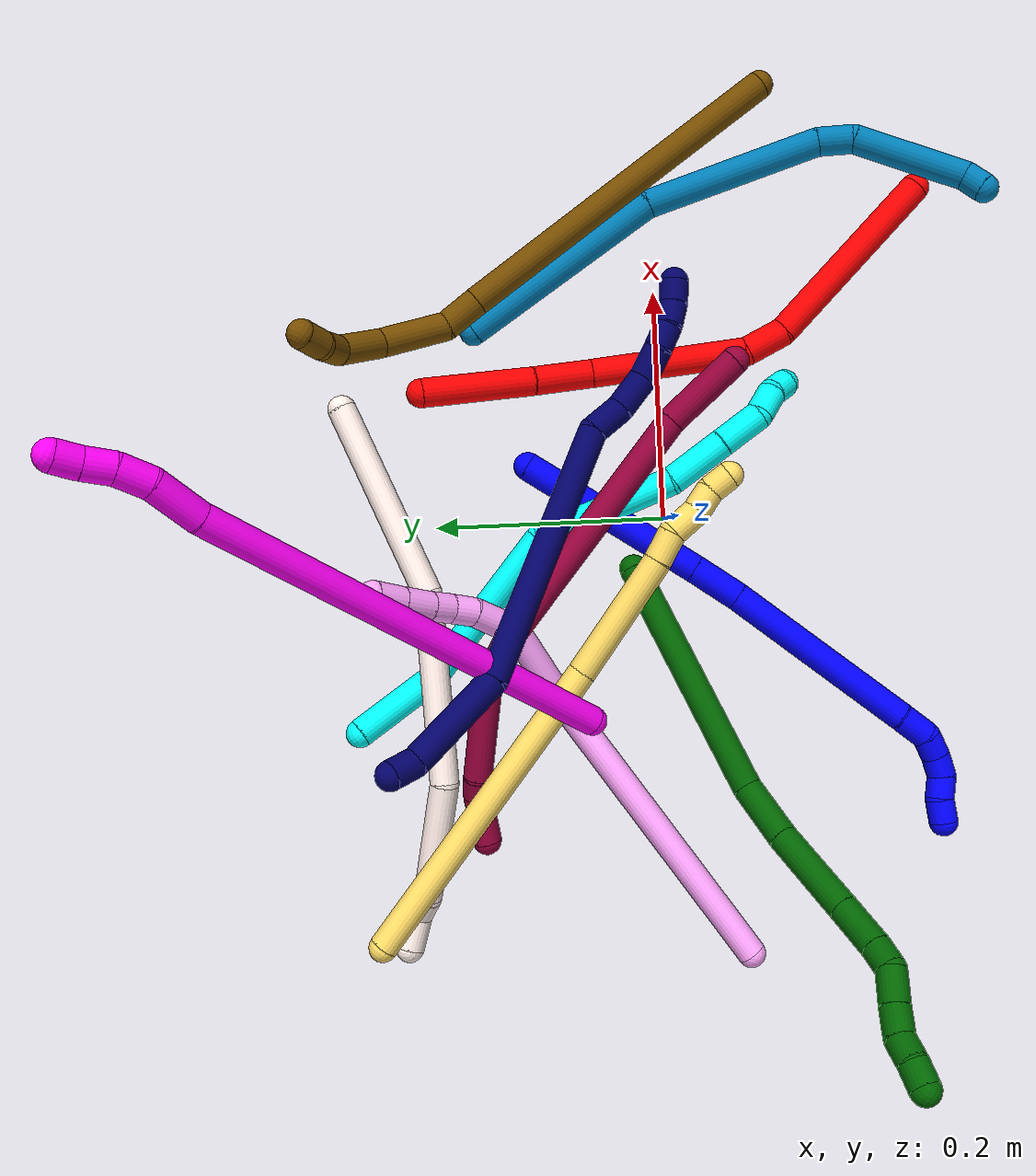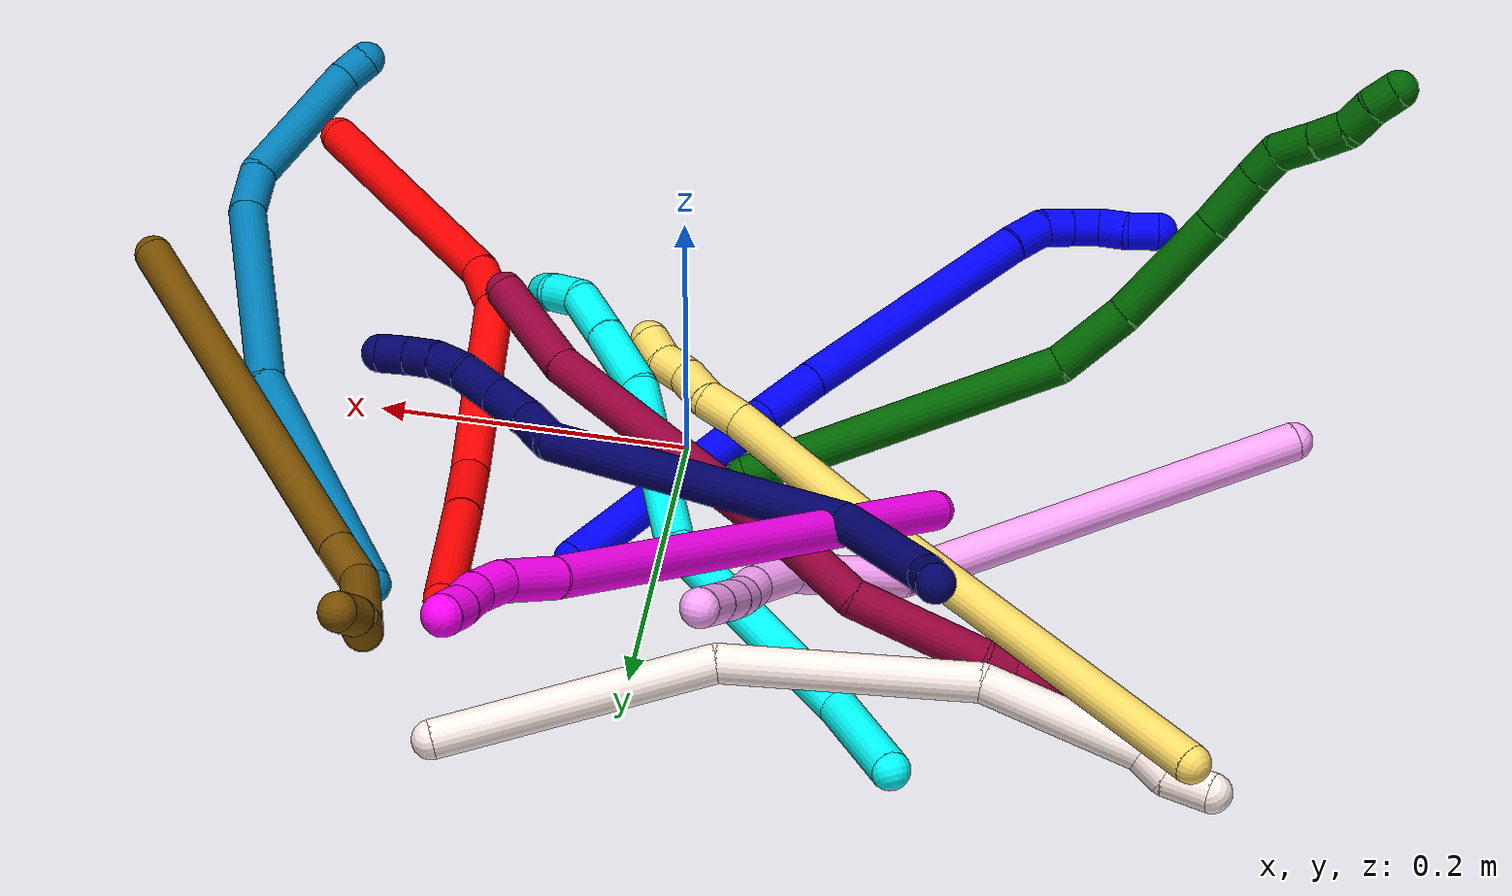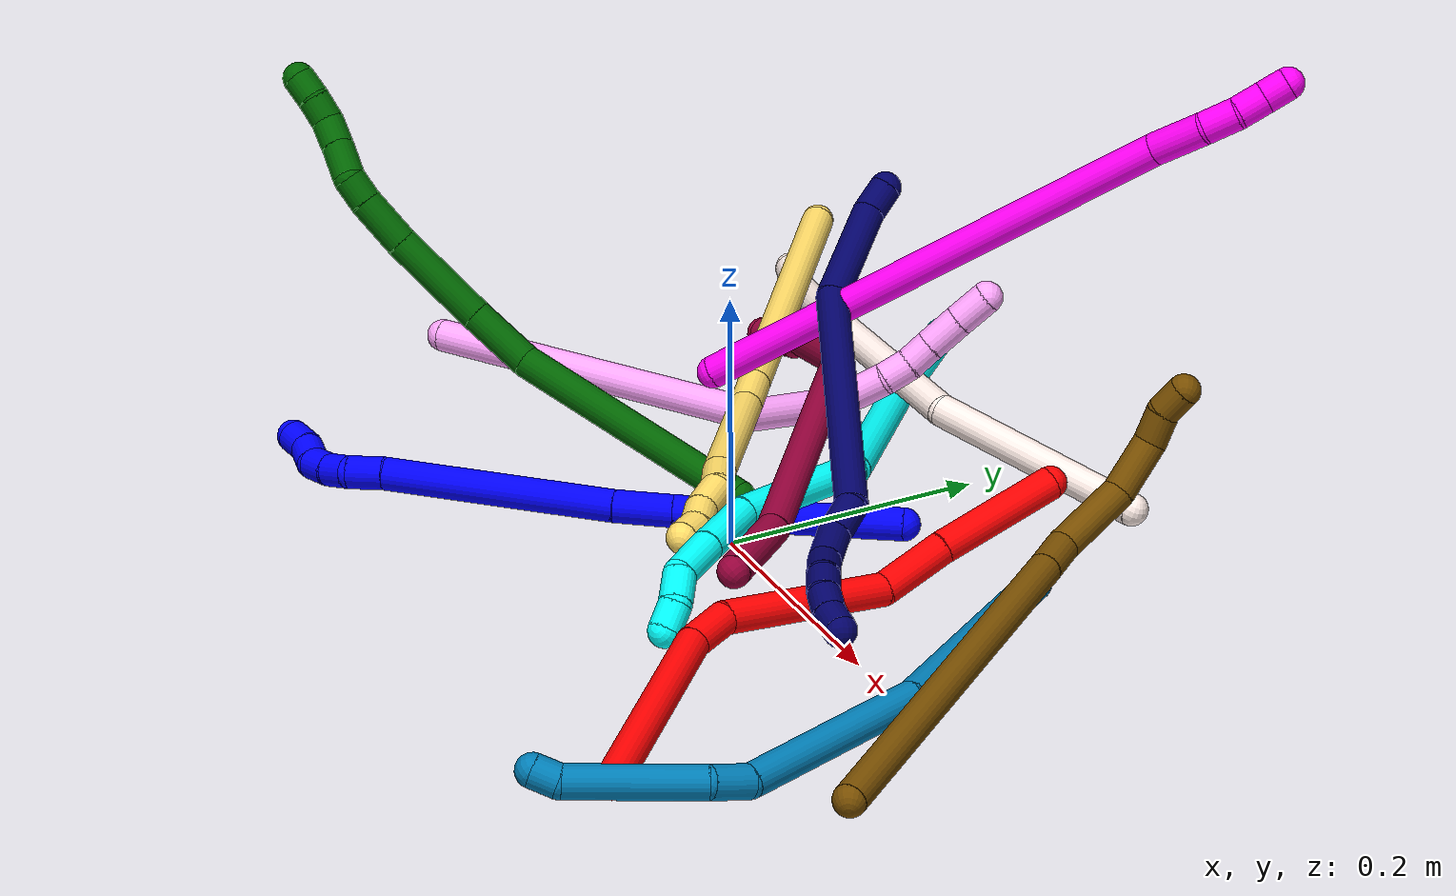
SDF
<sdf version="1.7">
 <world name="default">
  <plugin name="TubeGeneratorPlugin" filename="libtube_generator_plugin.so"/>
  <model name="photoneo_s_sensor">
   <static>1</static>
   <pose>0 0 2 1.57079 1.57079 3.14159</pose>
   <link name="link">
    <inertial><mass>0.1</mass></inertial>
    <sensor name="sensor" type="depth">
     <update_rate>30</update_rate>
     <camera>
      <horizontal_fov>1.22</horizontal_fov>
      <image><width>1920</width><height>1200</height><format>B8G8R8</format></image>
      <clip><near>0.1</near><far>4</far></clip>
      <depth_camera><output>points</output></depth_camera>
     </camera>
     <plugin name="camera_plugin" filename="libgazebo_ros_depth_camera.so">
      <baseline>0.2</baseline>
      <alwaysOn>1</alwaysOn>
      <updateRate>0.0</updateRate>
      <cameraName>camera_ir</cameraName>
      <imageTopicName>/camera/color/image_raw</imageTopicName>
      <cameraInfoTopicName>/camera/color/camera_info</cameraInfoTopicName>
      <depthImageTopicName>/camera/depth/image_raw</depthImageTopicName>
      <depthImageCameraInfoTopicName>/camera/depth/camera_info</depthImageCameraInfoTopicName>
      <pointCloudTopicName>/camera/depth/points</pointCloudTopicName>
      <frameName>fr_optical</frameName>
      <pointCloudCutoff>0.1</pointCloudCutoff>
      <pointCloudCutoffMax>2.0</pointCloudCutoffMax>
      <distortionK1>0</distortionK1>
      <distortionK2>0</distortionK2>
      <distortionK3>0</distortionK3>
      <distortionT1>0</distortionT1>
      <distortionT2>0</distortionT2>
      <CxPrime>0</CxPrime>
      <Cx>0</Cx>
      <Cy>0</Cy>
      <focalLength>0</focalLength>
      <hackBaseline>0</hackBaseline>
     </plugin>
    </sensor>
   </link>
  </model>
  <gravity>0 0 -9.8</gravity>
  <magnetic_field>6e-06 2.3e-05 -4.2e-05</magnetic_field>
  <atmosphere type="adiabatic"/>
  <physics name="default_physics" default="0" type="ode">
   <max_step_size>0.003</max_step_size>
   <real_time_factor>1</real_time_factor>
   <real_time_update_rate>1000</real_time_update_rate>
   <max_contacts>10000</max_contacts>
   <ode>
    <solver>
     <type>quick</type>
     <iters>100</iters>
     <sor>1.3</sor>
     <use_dynamic_moi_rescaling>0</use_dynamic_moi_rescaling>
    </solver>
    <constraints>
     <contact_max_correcting_vel>0</contact_max_correcting_vel>
     <contact_surface_layer>0.001</contact_surface_layer>
     <cfm>0</cfm>
     <erp>0.2</erp>
    </constraints>
   </ode>
  </physics>
  <scene><ambient>0.4 0.4 0.4 1</ambient><background>0.7 0.7 0.7 1</background><shadows>0</shadows></scene>
  <audio><device>default</device></audio>
  <spherical_coordinates>
   <surface_model>EARTH_WGS84</surface_model>
   <latitude_deg>0</latitude_deg>
   <longitude_deg>0</longitude_deg>
   <elevation>0</elevation>
   <heading_deg>0</heading_deg>
  </spherical_coordinates>
  <model name="bin">
   <static>1</static>
   <link name="bottom">
    <collision name="collision-bottom">
     <pose>0 0 -0.01 0 -0 0</pose>
     <geometry><box><size>0.8 0.6 0.02</size></box></geometry>
     <surface>
      <friction><ode><mu>100</mu><mu2>100</mu2></ode></friction>
      <contact><collide_bitmask>65535</collide_bitmask></contact>
     </surface>
    </collision>
   </link>
   <link name="west_wall">
    <collision name="collision-west_wall">
     <pose>-0.41 0 0.1 0 -0 0</pose>
     <geometry><box><size>0.02 0.6 0.2</size></box></geometry>
     <surface>
      <friction><ode><mu>100</mu><mu2>100</mu2></ode></friction>
      <contact><collide_bitmask>65535</collide_bitmask></contact>
     </surface>
    </collision>
   </link>
   <link name="east_wall">
    <collision name="collision-east_wall">
     <pose>0.41 0 0.1 0 -0 0</pose>
     <geometry><box><size>0.02 0.6 0.2</size></box></geometry>
     <surface>
      <friction><ode><mu>100</mu><mu2>100</mu2></ode></friction>
      <contact><collide_bitmask>65535</collide_bitmask></contact>
     </surface>
    </collision>
   </link>
   <link name="south_wall">
    <collision name="collision-south_wall">
     <pose>0 -0.31 0.1 0 -0 0</pose>
     <geometry><box><size>0.8 0.02 0.2</size></box></geometry>
     <surface>
      <friction><ode><mu>100</mu><mu2>100</mu2></ode></friction>
      <contact><collide_bitmask>65535</collide_bitmask></contact>
     </surface>
    </collision>
   </link>
   <link name="north_wall">
    <collision name="collision-north_wall">
     <pose>0 0.31 0.1 0 -0 0</pose>
     <geometry><box><size>0.8 0.02 0.2</size></box></geometry>
     <surface>
      <friction><ode><mu>100</mu><mu2>100</mu2></ode></friction>
      <contact><collide_bitmask>65535</collide_bitmask></contact>
     </surface>
    </collision>
   </link>
  </model>
  <model name="1">
   <static>0</static>
   <link name="1">
    <collision name="collision-cylinder-e_1_1_4">
     <pose>-0.033363 -0.058896 0.0524 0.843702 -0.400361 -0.181618</pose>
     <geometry><cylinder><radius>0.0125</radius><length>0.171202</length></cylinder></geometry>
     <surface>
      <friction><ode><mu>1.16</mu><mu2>1.16</mu2><slip1>0</slip1><slip2>0</slip2></ode></friction>
      <contact><ode><kp>1e+06</kp><kd>1</kd><max_vel>0</max_vel><min_depth>0.001</min_depth></ode></contact>
     </surface>
    </collision>
    <visual name="visual-cylinder-e_1_1_4">
     <pose>-0.033363 -0.058896 0.0524 0.843702 -0.400361 -0.181618</pose>
     <geometry><cylinder><radius>0.0125</radius><length>0.171202</length></cylinder></geometry>
     <material><ambient>0 0 1 1</ambient></material>
    </visual>
    <collision name="collision-cylinder-e_2_4_5">
     <pose>-0.075448 -0.132735 0.119032 0.809714 -0.399863 -0.173239</pose>
     <geometry><cylinder><radius>0.0125</radius><length>0.044808</length></cylinder></geometry>
     <surface>
      <friction><ode><mu>1.16</mu><mu2>1.16</mu2><slip1>0</slip1><slip2>0</slip2></ode></friction>
      <contact><ode><kp>1e+06</kp><kd>1</kd><max_vel>0</max_vel><min_depth>0.001</min_depth></ode></contact>
     </surface>
    </collision>
    <visual name="visual-cylinder-e_2_4_5">
     <pose>-0.075448 -0.132735 0.119032 0.809714 -0.399863 -0.173239</pose>
     <geometry><cylinder><radius>0.0125</radius><length>0.044808</length></cylinder></geometry>
     <material><ambient>0 0 1 1</ambient></material>
    </visual>
    <collision name="collision-cylinder-e_3_5_6">
     <pose>-0.118983 -0.202096 0.193052 0.738432 -0.40662 -0.159214</pose>
     <geometry><cylinder><radius>0.0125</radius><length>0.176043</length></cylinder></geometry>
     <surface>
      <friction><ode><mu>1.16</mu><mu2>1.16</mu2><slip1>0</slip1><slip2>0</slip2></ode></friction>
      <contact><ode><kp>1e+06</kp><kd>1</kd><max_vel>0</max_vel><min_depth>0.001</min_depth></ode></contact>
     </surface>
    </collision>
    <visual name="visual-cylinder-e_3_5_6">
     <pose>-0.118983 -0.202096 0.193052 0.738432 -0.40662 -0.159214</pose>
     <geometry><cylinder><radius>0.0125</radius><length>0.176043</length></cylinder></geometry>
     <material><ambient>0 0 1 1</ambient></material>
    </visual>
    <collision name="collision-cylinder-e_4_6_7">
     <pose>-0.160562 -0.265193 0.261255 0.800693 -0.510248 -0.219858</pose>
     <geometry><cylinder><radius>0.0125</radius><length>0.027708</length></cylinder></geometry>
     <surface>
      <friction><ode><mu>1.16</mu><mu2>1.16</mu2><slip1>0</slip1><slip2>0</slip2></ode></friction>
      <contact><ode><kp>1e+06</kp><kd>1</kd><max_vel>0</max_vel><min_depth>0.001</min_depth></ode></contact>
     </surface>
    </collision>
    <visual name="visual-cylinder-e_4_6_7">
     <pose>-0.160562 -0.265193 0.261255 0.800693 -0.510248 -0.219858</pose>
     <geometry><cylinder><radius>0.0125</radius><length>0.027708</length></cylinder></geometry>
     <material><ambient>0 0 1 1</ambient></material>
    </visual>
    <collision name="collision-cylinder-e_5_7_8">
     <pose>-0.174936 -0.276407 0.275809 0.391871 -0.853148 -0.179926</pose>
     <geometry><cylinder><radius>0.0125</radius><length>0.020198</length></cylinder></geometry>
     <surface>
      <friction><ode><mu>1.16</mu><mu2>1.16</mu2><slip1>0</slip1><slip2>0</slip2></ode></friction>
      <contact><ode><kp>1e+06</kp><kd>1</kd><max_vel>0</max_vel><min_depth>0.001</min_depth></ode></contact>
     </surface>
    </collision>
    <visual name="visual-cylinder-e_5_7_8">
     <pose>-0.174936 -0.276407 0.275809 0.391871 -0.853148 -0.179926</pose>
     <geometry><cylinder><radius>0.0125</radius><length>0.020198</length></cylinder></geometry>
     <material><ambient>0 0 1 1</ambient></material>
    </visual>
    <collision name="collision-cylinder-e_6_8_9">
     <pose>-0.18952 -0.279675 0.289093 0.101917 -0.770704 -0.041371</pose>
     <geometry><cylinder><radius>0.0125</radius><length>0.020026</length></cylinder></geometry>
     <surface>
      <friction><ode><mu>1.16</mu><mu2>1.16</mu2><slip1>0</slip1><slip2>0</slip2></ode></friction>
      <contact><ode><kp>1e+06</kp><kd>1</kd><max_vel>0</max_vel><min_depth>0.001</min_depth></ode></contact>
     </surface>
    </collision>
    <visual name="visual-cylinder-e_6_8_9">
     <pose>-0.18952 -0.279675 0.289093 0.101917 -0.770704 -0.041371</pose>
     <geometry><cylinder><radius>0.0125</radius><length>0.020026</length></cylinder></geometry>
     <material><ambient>0 0 1 1</ambient></material>
    </visual>
    <collision name="collision-cylinder-e_7_9_10">
     <pose>-0.201547 -0.276519 0.303953 -0.466682 -0.529281 0.128638</pose>
     <geometry><cylinder><radius>0.0125</radius><length>0.020013</length></cylinder></geometry>
     <surface>
      <friction><ode><mu>1.16</mu><mu2>1.16</mu2><slip1>0</slip1><slip2>0</slip2></ode></friction>
      <contact><ode><kp>1e+06</kp><kd>1</kd><max_vel>0</max_vel><min_depth>0.001</min_depth></ode></contact>
     </surface>
    </collision>
    <visual name="visual-cylinder-e_7_9_10">
     <pose>-0.201547 -0.276519 0.303953 -0.466682 -0.529281 0.128638</pose>
     <geometry><cylinder><radius>0.0125</radius><length>0.020013</length></cylinder></geometry>
     <material><ambient>0 0 1 1</ambient></material>
    </visual>
    <collision name="collision-cylinder-e_8_10_2">
     <pose>-0.212789 -0.271727 0.319471 -0.11559 -0.667277 0.040102</pose>
     <geometry><cylinder><radius>0.0125</radius><length>0.020003</length></cylinder></geometry>
     <surface>
      <friction><ode><mu>1.16</mu><mu2>1.16</mu2><slip1>0</slip1><slip2>0</slip2></ode></friction>
      <contact><ode><kp>1e+06</kp><kd>1</kd><max_vel>0</max_vel><min_depth>0.001</min_depth></ode></contact>
     </surface>
    </collision>
    <visual name="visual-cylinder-e_8_10_2">
     <pose>-0.212789 -0.271727 0.319471 -0.11559 -0.667277 0.040102</pose>
     <geometry><cylinder><radius>0.0125</radius><length>0.020003</length></cylinder></geometry>
     <material><ambient>0 0 1 1</ambient></material>
    </visual>
    <collision name="collision-sphere-2">
     <pose>-0.218978 -0.270821 0.327274 0 -0 0</pose>
     <geometry><sphere><radius>0.0125</radius></sphere></geometry>
     <surface>
      <friction><ode><mu>1.16</mu><mu2>1.16</mu2><slip1>0</slip1><slip2>0</slip2></ode></friction>
      <contact><ode><kp>1e+06</kp><kd>1</kd><max_vel>0</max_vel><min_depth>0.001</min_depth></ode></contact>
     </surface>
    </collision>
    <visual name="visual-sphere-2">
     <pose>-0.218978 -0.270821 0.327274 0 -0 0</pose>
     <geometry><sphere><radius>0.0125</radius></sphere></geometry>
     <material><ambient>0 0 1 1</ambient></material>
    </visual>
    <collision name="collision-sphere-10">
     <pose>-0.2066 -0.272633 0.311667 0 -0 0</pose>
     <geometry><sphere><radius>0.0125</radius></sphere></geometry>
     <surface>
      <friction><ode><mu>1.16</mu><mu2>1.16</mu2><slip1>0</slip1><slip2>0</slip2></ode></friction>
      <contact><ode><kp>1e+06</kp><kd>1</kd><max_vel>0</max_vel><min_depth>0.001</min_depth></ode></contact>
     </surface>
    </collision>
    <visual name="visual-sphere-10">
     <pose>-0.2066 -0.272633 0.311667 0 -0 0</pose>
     <geometry><sphere><radius>0.0125</radius></sphere></geometry>
     <material><ambient>0 0 1 1</ambient></material>
    </visual>
    <collision name="collision-sphere-9">
     <pose>-0.196495 -0.280405 0.29624 0 -0 0</pose>
     <geometry><sphere><radius>0.0125</radius></sphere></geometry>
     <surface>
      <friction><ode><mu>1.16</mu><mu2>1.16</mu2><slip1>0</slip1><slip2>0</slip2></ode></friction>
      <contact><ode><kp>1e+06</kp><kd>1</kd><max_vel>0</max_vel><min_depth>0.001</min_depth></ode></contact>
     </surface>
    </collision>
    <visual name="visual-sphere-9">
     <pose>-0.196495 -0.280405 0.29624 0 -0 0</pose>
     <geometry><sphere><radius>0.0125</radius></sphere></geometry>
     <material><ambient>0 0 1 1</ambient></material>
    </visual>
    <collision name="collision-sphere-4">
     <pose>-0.066726 -0.117792 0.104799 0 -0 0</pose>
     <geometry><sphere><radius>0.0125</radius></sphere></geometry>
     <surface>
      <friction><ode><mu>1.16</mu><mu2>1.16</mu2><slip1>0</slip1><slip2>0</slip2></ode></friction>
      <contact><ode><kp>1e+06</kp><kd>1</kd><max_vel>0</max_vel><min_depth>0.001</min_depth></ode></contact>
     </surface>
    </collision>
    <visual name="visual-sphere-4">
     <pose>-0.066726 -0.117792 0.104799 0 -0 0</pose>
     <geometry><sphere><radius>0.0125</radius></sphere></geometry>
     <material><ambient>0 0 1 1</ambient></material>
    </visual>
    <collision name="collision-sphere-1">
     <geometry><sphere><radius>0.0125</radius></sphere></geometry>
     <surface>
      <friction><ode><mu>1.16</mu><mu2>1.16</mu2><slip1>0</slip1><slip2>0</slip2></ode></friction>
      <contact><ode><kp>1e+06</kp><kd>1</kd><max_vel>0</max_vel><min_depth>0.001</min_depth></ode></contact>
     </surface>
    </collision>
    <visual name="visual-sphere-1">
     <geometry><sphere><radius>0.0125</radius></sphere></geometry>
     <material><ambient>0 0 1 1</ambient></material>
    </visual>
    <collision name="collision-sphere-8">
     <pose>-0.182544 -0.278944 0.281947 0 -0 0</pose>
     <geometry><sphere><radius>0.0125</radius></sphere></geometry>
     <surface>
      <friction><ode><mu>1.16</mu><mu2>1.16</mu2><slip1>0</slip1><slip2>0</slip2></ode></friction>
      <contact><ode><kp>1e+06</kp><kd>1</kd><max_vel>0</max_vel><min_depth>0.001</min_depth></ode></contact>
     </surface>
    </collision>
    <visual name="visual-sphere-8">
     <pose>-0.182544 -0.278944 0.281947 0 -0 0</pose>
     <geometry><sphere><radius>0.0125</radius></sphere></geometry>
     <material><ambient>0 0 1 1</ambient></material>
    </visual>
    <collision name="collision-sphere-5">
     <pose>-0.08417 -0.147678 0.133266 0 -0 0</pose>
     <geometry><sphere><radius>0.0125</radius></sphere></geometry>
     <surface>
      <friction><ode><mu>1.16</mu><mu2>1.16</mu2><slip1>0</slip1><slip2>0</slip2></ode></friction>
      <contact><ode><kp>1e+06</kp><kd>1</kd><max_vel>0</max_vel><min_depth>0.001</min_depth></ode></contact>
     </surface>
    </collision>
    <visual name="visual-sphere-5">
     <pose>-0.08417 -0.147678 0.133266 0 -0 0</pose>
     <geometry><sphere><radius>0.0125</radius></sphere></geometry>
     <material><ambient>0 0 1 1</ambient></material>
    </visual>
    <collision name="collision-sphere-6">
     <pose>-0.153796 -0.256515 0.252838 0 -0 0</pose>
     <geometry><sphere><radius>0.0125</radius></sphere></geometry>
     <surface>
      <friction><ode><mu>1.16</mu><mu2>1.16</mu2><slip1>0</slip1><slip2>0</slip2></ode></friction>
      <contact><ode><kp>1e+06</kp><kd>1</kd><max_vel>0</max_vel><min_depth>0.001</min_depth></ode></contact>
     </surface>
    </collision>
    <visual name="visual-sphere-6">
     <pose>-0.153796 -0.256515 0.252838 0 -0 0</pose>
     <geometry><sphere><radius>0.0125</radius></sphere></geometry>
     <material><ambient>0 0 1 1</ambient></material>
    </visual>
    <collision name="collision-sphere-7">
     <pose>-0.167328 -0.273871 0.269672 0 -0 0</pose>
     <geometry><sphere><radius>0.0125</radius></sphere></geometry>
     <surface>
      <friction><ode><mu>1.16</mu><mu2>1.16</mu2><slip1>0</slip1><slip2>0</slip2></ode></friction>
      <contact><ode><kp>1e+06</kp><kd>1</kd><max_vel>0</max_vel><min_depth>0.001</min_depth></ode></contact>
     </surface>
    </collision>
    <visual name="visual-sphere-7">
     <pose>-0.167328 -0.273871 0.269672 0 -0 0</pose>
     <geometry><sphere><radius>0.0125</radius></sphere></geometry>
     <material><ambient>0 0 1 1</ambient></material>
    </visual>
    <inertial>
     <pose>-0.100212 -0.162218 0.158724 0 -0 0</pose>
     <mass>0.5</mass>
     <inertia>
      <ixx>0.000662</ixx>
      <ixy>0</ixy>
      <ixz>0</ixz>
      <iyy>0.00051</iyy>
      <iyz>0</iyz>
      <izz>0.000968</izz>
     </inertia>
    </inertial>
   </link>
   <pose>0.050886 0.116939 0.011491 0.2063 -0.865923 0.051608</pose>
  </model>
  <model name="2">
   <static>0</static>
   <link name="2">
    <collision name="collision-cylinder-e_1_1_4">
     <pose>-0.037078 0.033559 -0.071288 -2.70161 -0.439841 1.57046</pose>
     <geometry><cylinder><radius>0.0125</radius><length>0.174161</length></cylinder></geometry>
     <surface>
      <friction><ode><mu>1.16</mu><mu2>1.16</mu2><slip1>0</slip1><slip2>0</slip2></ode></friction>
      <contact><ode><kp>1e+06</kp><kd>1</kd><max_vel>0</max_vel><min_depth>0.001</min_depth></ode></contact>
     </surface>
    </collision>
    <visual name="visual-cylinder-e_1_1_4">
     <pose>-0.037078 0.033559 -0.071288 -2.70161 -0.439841 1.57046</pose>
     <geometry><cylinder><radius>0.0125</radius><length>0.174161</length></cylinder></geometry>
     <material><ambient>1 0 0 1</ambient></material>
    </visual>
    <collision name="collision-cylinder-e_2_4_5">
     <pose>-0.079012 0.079034 -0.155837 -2.40962 -0.265891 0.67147</pose>
     <geometry><cylinder><radius>0.0125</radius><length>0.036954</length></cylinder></geometry>
     <surface>
      <friction><ode><mu>1.16</mu><mu2>1.16</mu2><slip1>0</slip1><slip2>0</slip2></ode></friction>
      <contact><ode><kp>1e+06</kp><kd>1</kd><max_vel>0</max_vel><min_depth>0.001</min_depth></ode></contact>
     </surface>
    </collision>
    <visual name="visual-cylinder-e_2_4_5">
     <pose>-0.079012 0.079034 -0.155837 -2.40962 -0.265891 0.67147</pose>
     <geometry><cylinder><radius>0.0125</radius><length>0.036954</length></cylinder></geometry>
     <material><ambient>1 0 0 1</ambient></material>
    </visual>
    <collision name="collision-cylinder-e_3_5_6">
     <pose>-0.075128 0.144141 -0.210238 -2.22912 0.129239 -0.262194</pose>
     <geometry><cylinder><radius>0.0125</radius><length>0.13562</length></cylinder></geometry>
     <surface>
      <friction><ode><mu>1.16</mu><mu2>1.16</mu2><slip1>0</slip1><slip2>0</slip2></ode></friction>
      <contact><ode><kp>1e+06</kp><kd>1</kd><max_vel>0</max_vel><min_depth>0.001</min_depth></ode></contact>
     </surface>
    </collision>
    <visual name="visual-cylinder-e_3_5_6">
     <pose>-0.075128 0.144141 -0.210238 -2.22912 0.129239 -0.262194</pose>
     <geometry><cylinder><radius>0.0125</radius><length>0.13562</length></cylinder></geometry>
     <material><ambient>1 0 0 1</ambient></material>
    </visual>
    <collision name="collision-cylinder-e_4_6_7">
     <pose>-0.073615 0.221529 -0.261952 -1.98279 -0.267109 0.405043</pose>
     <geometry><cylinder><radius>0.0125</radius><length>0.054754</length></cylinder></geometry>
     <surface>
      <friction><ode><mu>1.16</mu><mu2>1.16</mu2><slip1>0</slip1><slip2>0</slip2></ode></friction>
      <contact><ode><kp>1e+06</kp><kd>1</kd><max_vel>0</max_vel><min_depth>0.001</min_depth></ode></contact>
     </surface>
    </collision>
    <visual name="visual-cylinder-e_4_6_7">
     <pose>-0.073615 0.221529 -0.261952 -1.98279 -0.267109 0.405043</pose>
     <geometry><cylinder><radius>0.0125</radius><length>0.054754</length></cylinder></geometry>
     <material><ambient>1 0 0 1</ambient></material>
    </visual>
    <collision name="collision-cylinder-e_5_7_2">
     <pose>-0.090209 0.289639 -0.292774 -2.00284 -0.191357 0.29765</pose>
     <geometry><cylinder><radius>0.0125</radius><length>0.09851</length></cylinder></geometry>
     <surface>
      <friction><ode><mu>1.16</mu><mu2>1.16</mu2><slip1>0</slip1><slip2>0</slip2></ode></friction>
      <contact><ode><kp>1e+06</kp><kd>1</kd><max_vel>0</max_vel><min_depth>0.001</min_depth></ode></contact>
     </surface>
    </collision>
    <visual name="visual-cylinder-e_5_7_2">
     <pose>-0.090209 0.289639 -0.292774 -2.00284 -0.191357 0.29765</pose>
     <geometry><cylinder><radius>0.0125</radius><length>0.09851</length></cylinder></geometry>
     <material><ambient>1 0 0 1</ambient></material>
    </visual>
    <collision name="collision-sphere-2">
     <pose>-0.099577 0.333552 -0.313022 0 -0 0</pose>
     <geometry><sphere><radius>0.0125</radius></sphere></geometry>
     <surface>
      <friction><ode><mu>1.16</mu><mu2>1.16</mu2><slip1>0</slip1><slip2>0</slip2></ode></friction>
      <contact><ode><kp>1e+06</kp><kd>1</kd><max_vel>0</max_vel><min_depth>0.001</min_depth></ode></contact>
     </surface>
    </collision>
    <visual name="visual-sphere-2">
     <pose>-0.099577 0.333552 -0.313022 0 -0 0</pose>
     <geometry><sphere><radius>0.0125</radius></sphere></geometry>
     <material><ambient>1 0 0 1</ambient></material>
    </visual>
    <collision name="collision-sphere-7">
     <pose>-0.080841 0.245726 -0.272526 0 -0 0</pose>
     <geometry><sphere><radius>0.0125</radius></sphere></geometry>
     <surface>
      <friction><ode><mu>1.16</mu><mu2>1.16</mu2><slip1>0</slip1><slip2>0</slip2></ode></friction>
      <contact><ode><kp>1e+06</kp><kd>1</kd><max_vel>0</max_vel><min_depth>0.001</min_depth></ode></contact>
     </surface>
    </collision>
    <visual name="visual-sphere-7">
     <pose>-0.080841 0.245726 -0.272526 0 -0 0</pose>
     <geometry><sphere><radius>0.0125</radius></sphere></geometry>
     <material><ambient>1 0 0 1</ambient></material>
    </visual>
    <collision name="collision-sphere-6">
     <pose>-0.066389 0.197333 -0.251378 0 -0 0</pose>
     <geometry><sphere><radius>0.0125</radius></sphere></geometry>
     <surface>
      <friction><ode><mu>1.16</mu><mu2>1.16</mu2><slip1>0</slip1><slip2>0</slip2></ode></friction>
      <contact><ode><kp>1e+06</kp><kd>1</kd><max_vel>0</max_vel><min_depth>0.001</min_depth></ode></contact>
     </surface>
    </collision>
    <visual name="visual-sphere-6">
     <pose>-0.066389 0.197333 -0.251378 0 -0 0</pose>
     <geometry><sphere><radius>0.0125</radius></sphere></geometry>
     <material><ambient>1 0 0 1</ambient></material>
    </visual>
    <collision name="collision-sphere-5">
     <pose>-0.083867 0.090949 -0.169098 0 -0 0</pose>
     <geometry><sphere><radius>0.0125</radius></sphere></geometry>
     <surface>
      <friction><ode><mu>1.16</mu><mu2>1.16</mu2><slip1>0</slip1><slip2>0</slip2></ode></friction>
      <contact><ode><kp>1e+06</kp><kd>1</kd><max_vel>0</max_vel><min_depth>0.001</min_depth></ode></contact>
     </surface>
    </collision>
    <visual name="visual-sphere-5">
     <pose>-0.083867 0.090949 -0.169098 0 -0 0</pose>
     <geometry><sphere><radius>0.0125</radius></sphere></geometry>
     <material><ambient>1 0 0 1</ambient></material>
    </visual>
    <collision name="collision-sphere-1">
     <geometry><sphere><radius>0.0125</radius></sphere></geometry>
     <surface>
      <friction><ode><mu>1.16</mu><mu2>1.16</mu2><slip1>0</slip1><slip2>0</slip2></ode></friction>
      <contact><ode><kp>1e+06</kp><kd>1</kd><max_vel>0</max_vel><min_depth>0.001</min_depth></ode></contact>
     </surface>
    </collision>
    <visual name="visual-sphere-1">
     <geometry><sphere><radius>0.0125</radius></sphere></geometry>
     <material><ambient>1 0 0 1</ambient></material>
    </visual>
    <collision name="collision-sphere-4">
     <pose>-0.074157 0.067119 -0.142576 0 -0 0</pose>
     <geometry><sphere><radius>0.0125</radius></sphere></geometry>
     <surface>
      <friction><ode><mu>1.16</mu><mu2>1.16</mu2><slip1>0</slip1><slip2>0</slip2></ode></friction>
      <contact><ode><kp>1e+06</kp><kd>1</kd><max_vel>0</max_vel><min_depth>0.001</min_depth></ode></contact>
     </surface>
    </collision>
    <visual name="visual-sphere-4">
     <pose>-0.074157 0.067119 -0.142576 0 -0 0</pose>
     <geometry><sphere><radius>0.0125</radius></sphere></geometry>
     <material><ambient>1 0 0 1</ambient></material>
    </visual>
    <inertial>
     <pose>-0.064967 0.137952 -0.179742 0 -0 0</pose>
     <mass>0.5</mass>
     <inertia>
      <ixx>0.000676</ixx>
      <ixy>0</ixy>
      <ixz>0</ixz>
      <iyy>0.000334</iyy>
      <iyz>0</iyz>
      <izz>-0.000272</izz>
     </inertia>
    </inertial>
   </link>
   <pose>0.280103 -0.232331 0.011497 0.620139 0.934656 0.128819</pose>
  </model>
  <model name="3">
   <static>0</static>
   <link name="3">
    <collision name="collision-cylinder-e_1_1_4">
     <pose>0.023321 -0.019604 -0.023768 2.45191 0.647927 1.50348</pose>
     <geometry><cylinder><radius>0.0125</radius><length>0.077282</length></cylinder></geometry>
     <surface>
      <friction><ode><mu>1.16</mu><mu2>1.16</mu2><slip1>0</slip1><slip2>0</slip2></ode></friction>
      <contact><ode><kp>1e+06</kp><kd>1</kd><max_vel>0</max_vel><min_depth>0.001</min_depth></ode></contact>
     </surface>
    </collision>
    <visual name="visual-cylinder-e_1_1_4">
     <pose>0.023321 -0.019604 -0.023768 2.45191 0.647927 1.50348</pose>
     <geometry><cylinder><radius>0.0125</radius><length>0.077282</length></cylinder></geometry>
     <material><ambient>0.003922 1 0.996078 1</ambient></material>
    </visual>
    <collision name="collision-cylinder-e_2_4_5">
     <pose>0.061471 -0.082851 -0.110801 2.53771 0.190595 0.595544</pose>
     <geometry><cylinder><radius>0.0125</radius><length>0.156549</length></cylinder></geometry>
     <surface>
      <friction><ode><mu>1.16</mu><mu2>1.16</mu2><slip1>0</slip1><slip2>0</slip2></ode></friction>
      <contact><ode><kp>1e+06</kp><kd>1</kd><max_vel>0</max_vel><min_depth>0.001</min_depth></ode></contact>
     </surface>
    </collision>
    <visual name="visual-cylinder-e_2_4_5">
     <pose>0.061471 -0.082851 -0.110801 2.53771 0.190595 0.595544</pose>
     <geometry><cylinder><radius>0.0125</radius><length>0.156549</length></cylinder></geometry>
     <material><ambient>0.003922 1 0.996078 1</ambient></material>
    </visual>
    <collision name="collision-cylinder-e_3_5_6">
     <pose>0.106876 -0.1366 -0.22748 2.9546 0.512358 2.45404</pose>
     <geometry><cylinder><radius>0.0125</radius><length>0.124744</length></cylinder></geometry>
     <surface>
      <friction><ode><mu>1.16</mu><mu2>1.16</mu2><slip1>0</slip1><slip2>0</slip2></ode></friction>
      <contact><ode><kp>1e+06</kp><kd>1</kd><max_vel>0</max_vel><min_depth>0.001</min_depth></ode></contact>
     </surface>
    </collision>
    <visual name="visual-cylinder-e_3_5_6">
     <pose>0.106876 -0.1366 -0.22748 2.9546 0.512358 2.45404</pose>
     <geometry><cylinder><radius>0.0125</radius><length>0.124744</length></cylinder></geometry>
     <material><ambient>0.003922 1 0.996078 1</ambient></material>
    </visual>
    <collision name="collision-cylinder-e_4_6_7">
     <pose>0.14973 -0.158018 -0.301801 2.64564 0.476732 1.52967</pose>
     <geometry><cylinder><radius>0.0125</radius><length>0.053507</length></cylinder></geometry>
     <surface>
      <friction><ode><mu>1.16</mu><mu2>1.16</mu2><slip1>0</slip1><slip2>0</slip2></ode></friction>
      <contact><ode><kp>1e+06</kp><kd>1</kd><max_vel>0</max_vel><min_depth>0.001</min_depth></ode></contact>
     </surface>
    </collision>
    <visual name="visual-cylinder-e_4_6_7">
     <pose>0.14973 -0.158018 -0.301801 2.64564 0.476732 1.52967</pose>
     <geometry><cylinder><radius>0.0125</radius><length>0.053507</length></cylinder></geometry>
     <material><ambient>0.003922 1 0.996078 1</ambient></material>
    </visual>
    <collision name="collision-cylinder-e_5_7_8">
     <pose>0.171904 -0.178277 -0.337716 2.604 0.515401 1.52664</pose>
     <geometry><cylinder><radius>0.0125</radius><length>0.040162</length></cylinder></geometry>
     <surface>
      <friction><ode><mu>1.16</mu><mu2>1.16</mu2><slip1>0</slip1><slip2>0</slip2></ode></friction>
      <contact><ode><kp>1e+06</kp><kd>1</kd><max_vel>0</max_vel><min_depth>0.001</min_depth></ode></contact>
     </surface>
    </collision>
    <visual name="visual-cylinder-e_5_7_8">
     <pose>0.171904 -0.178277 -0.337716 2.604 0.515401 1.52664</pose>
     <geometry><cylinder><radius>0.0125</radius><length>0.040162</length></cylinder></geometry>
     <material><ambient>0.003922 1 0.996078 1</ambient></material>
    </visual>
    <collision name="collision-cylinder-e_6_8_9">
     <pose>0.187953 -0.19773 -0.357911 2.02939 0.483438 0.755253</pose>
     <geometry><cylinder><radius>0.0125</radius><length>0.026467</length></cylinder></geometry>
     <surface>
      <friction><ode><mu>1.16</mu><mu2>1.16</mu2><slip1>0</slip1><slip2>0</slip2></ode></friction>
      <contact><ode><kp>1e+06</kp><kd>1</kd><max_vel>0</max_vel><min_depth>0.001</min_depth></ode></contact>
     </surface>
    </collision>
    <visual name="visual-cylinder-e_6_8_9">
     <pose>0.187953 -0.19773 -0.357911 2.02939 0.483438 0.755253</pose>
     <geometry><cylinder><radius>0.0125</radius><length>0.026467</length></cylinder></geometry>
     <material><ambient>0.003922 1 0.996078 1</ambient></material>
    </visual>
    <collision name="collision-cylinder-e_7_9_2">
     <pose>0.202407 -0.21455 -0.36522 1.89514 0.89468 1.17713</pose>
     <geometry><cylinder><radius>0.0125</radius><length>0.021288</length></cylinder></geometry>
     <surface>
      <friction><ode><mu>1.16</mu><mu2>1.16</mu2><slip1>0</slip1><slip2>0</slip2></ode></friction>
      <contact><ode><kp>1e+06</kp><kd>1</kd><max_vel>0</max_vel><min_depth>0.001</min_depth></ode></contact>
     </surface>
    </collision>
    <visual name="visual-cylinder-e_7_9_2">
     <pose>0.202407 -0.21455 -0.36522 1.89514 0.89468 1.17713</pose>
     <geometry><cylinder><radius>0.0125</radius><length>0.021288</length></cylinder></geometry>
     <material><ambient>0.003922 1 0.996078 1</ambient></material>
    </visual>
    <collision name="collision-sphere-2">
     <pose>0.21071 -0.220864 -0.367343 0 -0 0</pose>
     <geometry><sphere><radius>0.0125</radius></sphere></geometry>
     <surface>
      <friction><ode><mu>1.16</mu><mu2>1.16</mu2><slip1>0</slip1><slip2>0</slip2></ode></friction>
      <contact><ode><kp>1e+06</kp><kd>1</kd><max_vel>0</max_vel><min_depth>0.001</min_depth></ode></contact>
     </surface>
    </collision>
    <visual name="visual-sphere-2">
     <pose>0.21071 -0.220864 -0.367343 0 -0 0</pose>
     <geometry><sphere><radius>0.0125</radius></sphere></geometry>
     <material><ambient>0.003922 1 0.996078 1</ambient></material>
    </visual>
    <collision name="collision-sphere-9">
     <pose>0.194104 -0.208237 -0.363098 0 -0 0</pose>
     <geometry><sphere><radius>0.0125</radius></sphere></geometry>
     <surface>
      <friction><ode><mu>1.16</mu><mu2>1.16</mu2><slip1>0</slip1><slip2>0</slip2></ode></friction>
      <contact><ode><kp>1e+06</kp><kd>1</kd><max_vel>0</max_vel><min_depth>0.001</min_depth></ode></contact>
     </surface>
    </collision>
    <visual name="visual-sphere-9">
     <pose>0.194104 -0.208237 -0.363098 0 -0 0</pose>
     <geometry><sphere><radius>0.0125</radius></sphere></geometry>
     <material><ambient>0.003922 1 0.996078 1</ambient></material>
    </visual>
    <collision name="collision-sphere-4">
     <pose>0.046643 -0.039208 -0.047537 0 -0 0</pose>
     <geometry><sphere><radius>0.0125</radius></sphere></geometry>
     <surface>
      <friction><ode><mu>1.16</mu><mu2>1.16</mu2><slip1>0</slip1><slip2>0</slip2></ode></friction>
      <contact><ode><kp>1e+06</kp><kd>1</kd><max_vel>0</max_vel><min_depth>0.001</min_depth></ode></contact>
     </surface>
    </collision>
    <visual name="visual-sphere-4">
     <pose>0.046643 -0.039208 -0.047537 0 -0 0</pose>
     <geometry><sphere><radius>0.0125</radius></sphere></geometry>
     <material><ambient>0.003922 1 0.996078 1</ambient></material>
    </visual>
    <collision name="collision-sphere-1">
     <geometry><sphere><radius>0.0125</radius></sphere></geometry>
     <surface>
      <friction><ode><mu>1.16</mu><mu2>1.16</mu2><slip1>0</slip1><slip2>0</slip2></ode></friction>
      <contact><ode><kp>1e+06</kp><kd>1</kd><max_vel>0</max_vel><min_depth>0.001</min_depth></ode></contact>
     </surface>
    </collision>
    <visual name="visual-sphere-1">
     <geometry><sphere><radius>0.0125</radius></sphere></geometry>
     <material><ambient>0.003922 1 0.996078 1</ambient></material>
    </visual>
    <collision name="collision-sphere-8">
     <pose>0.181802 -0.187224 -0.352724 0 -0 0</pose>
     <geometry><sphere><radius>0.0125</radius></sphere></geometry>
     <surface>
      <friction><ode><mu>1.16</mu><mu2>1.16</mu2><slip1>0</slip1><slip2>0</slip2></ode></friction>
      <contact><ode><kp>1e+06</kp><kd>1</kd><max_vel>0</max_vel><min_depth>0.001</min_depth></ode></contact>
     </surface>
    </collision>
    <visual name="visual-sphere-8">
     <pose>0.181802 -0.187224 -0.352724 0 -0 0</pose>
     <geometry><sphere><radius>0.0125</radius></sphere></geometry>
     <material><ambient>0.003922 1 0.996078 1</ambient></material>
    </visual>
    <collision name="collision-sphere-5">
     <pose>0.0763 -0.126493 -0.174065 0 -0 0</pose>
     <geometry><sphere><radius>0.0125</radius></sphere></geometry>
     <surface>
      <friction><ode><mu>1.16</mu><mu2>1.16</mu2><slip1>0</slip1><slip2>0</slip2></ode></friction>
      <contact><ode><kp>1e+06</kp><kd>1</kd><max_vel>0</max_vel><min_depth>0.001</min_depth></ode></contact>
     </surface>
    </collision>
    <visual name="visual-sphere-5">
     <pose>0.0763 -0.126493 -0.174065 0 -0 0</pose>
     <geometry><sphere><radius>0.0125</radius></sphere></geometry>
     <material><ambient>0.003922 1 0.996078 1</ambient></material>
    </visual>
    <collision name="collision-sphere-6">
     <pose>0.137453 -0.146706 -0.280895 0 -0 0</pose>
     <geometry><sphere><radius>0.0125</radius></sphere></geometry>
     <surface>
      <friction><ode><mu>1.16</mu><mu2>1.16</mu2><slip1>0</slip1><slip2>0</slip2></ode></friction>
      <contact><ode><kp>1e+06</kp><kd>1</kd><max_vel>0</max_vel><min_depth>0.001</min_depth></ode></contact>
     </surface>
    </collision>
    <visual name="visual-sphere-6">
     <pose>0.137453 -0.146706 -0.280895 0 -0 0</pose>
     <geometry><sphere><radius>0.0125</radius></sphere></geometry>
     <material><ambient>0.003922 1 0.996078 1</ambient></material>
    </visual>
    <collision name="collision-sphere-7">
     <pose>0.162007 -0.16933 -0.322708 0 -0 0</pose>
     <geometry><sphere><radius>0.0125</radius></sphere></geometry>
     <surface>
      <friction><ode><mu>1.16</mu><mu2>1.16</mu2><slip1>0</slip1><slip2>0</slip2></ode></friction>
      <contact><ode><kp>1e+06</kp><kd>1</kd><max_vel>0</max_vel><min_depth>0.001</min_depth></ode></contact>
     </surface>
    </collision>
    <visual name="visual-sphere-7">
     <pose>0.162007 -0.16933 -0.322708 0 -0 0</pose>
     <geometry><sphere><radius>0.0125</radius></sphere></geometry>
     <material><ambient>0.003922 1 0.996078 1</ambient></material>
    </visual>
    <inertial>
     <pose>0.097914 -0.113882 -0.189038 0 -0 0</pose>
     <mass>0.5</mass>
     <inertia>
      <ixx>0.000501</ixx>
      <ixy>0</ixy>
      <ixz>0</ixz>
      <iyy>0.000262</iyy>
      <iyz>0</iyz>
      <izz>3.2e-05</izz>
     </inertia>
    </inertial>
   </link>
   <pose>-0.173805 0.270595 0.032411 2.50755 0.739184 -1.90192</pose>
  </model>
  <model name="4">
   <static>0</static>
   <link name="4">
    <collision name="collision-cylinder-e_1_1_4">
     <pose>0.100253 0.055476 -0.077902 -2.52277 0.80896 -1.85874</pose>
     <geometry><cylinder><radius>0.0125</radius><length>0.277106</length></cylinder></geometry>
     <surface>
      <friction><ode><mu>1.16</mu><mu2>1.16</mu2><slip1>0</slip1><slip2>0</slip2></ode></friction>
      <contact><ode><kp>1e+06</kp><kd>1</kd><max_vel>0</max_vel><min_depth>0.001</min_depth></ode></contact>
     </surface>
    </collision>
    <visual name="visual-cylinder-e_1_1_4">
     <pose>0.100253 0.055476 -0.077902 -2.52277 0.80896 -1.85874</pose>
     <geometry><cylinder><radius>0.0125</radius><length>0.277106</length></cylinder></geometry>
     <material><ambient>1 0.65098 0.996078 1</ambient></material>
    </visual>
    <collision name="collision-cylinder-e_2_4_5">
     <pose>0.235254 0.11147 -0.176354 -3.11641 1.03658 -3.09743</pose>
     <geometry><cylinder><radius>0.0125</radius><length>0.080749</length></cylinder></geometry>
     <surface>
      <friction><ode><mu>1.16</mu><mu2>1.16</mu2><slip1>0</slip1><slip2>0</slip2></ode></friction>
      <contact><ode><kp>1e+06</kp><kd>1</kd><max_vel>0</max_vel><min_depth>0.001</min_depth></ode></contact>
     </surface>
    </collision>
    <visual name="visual-cylinder-e_2_4_5">
     <pose>0.235254 0.11147 -0.176354 -3.11641 1.03658 -3.09743</pose>
     <geometry><cylinder><radius>0.0125</radius><length>0.080749</length></cylinder></geometry>
     <material><ambient>1 0.65098 0.996078 1</ambient></material>
    </visual>
    <collision name="collision-cylinder-e_3_5_6">
     <pose>0.291294 0.114159 -0.197404 -1.79672 1.46654 -1.69391</pose>
     <geometry><cylinder><radius>0.0125</radius><length>0.042814</length></cylinder></geometry>
     <surface>
      <friction><ode><mu>1.16</mu><mu2>1.16</mu2><slip1>0</slip1><slip2>0</slip2></ode></friction>
      <contact><ode><kp>1e+06</kp><kd>1</kd><max_vel>0</max_vel><min_depth>0.001</min_depth></ode></contact>
     </surface>
    </collision>
    <visual name="visual-cylinder-e_3_5_6">
     <pose>0.291294 0.114159 -0.197404 -1.79672 1.46654 -1.69391</pose>
     <geometry><cylinder><radius>0.0125</radius><length>0.042814</length></cylinder></geometry>
     <material><ambient>1 0.65098 0.996078 1</ambient></material>
    </visual>
    <collision name="collision-cylinder-e_4_6_7">
     <pose>0.323199 0.118082 -0.195662 -0.663527 1.30897 -0.516846</pose>
     <geometry><cylinder><radius>0.0125</radius><length>0.021977</length></cylinder></geometry>
     <surface>
      <friction><ode><mu>1.16</mu><mu2>1.16</mu2><slip1>0</slip1><slip2>0</slip2></ode></friction>
      <contact><ode><kp>1e+06</kp><kd>1</kd><max_vel>0</max_vel><min_depth>0.001</min_depth></ode></contact>
     </surface>
    </collision>
    <visual name="visual-cylinder-e_4_6_7">
     <pose>0.323199 0.118082 -0.195662 -0.663527 1.30897 -0.516846</pose>
     <geometry><cylinder><radius>0.0125</radius><length>0.021977</length></cylinder></geometry>
     <material><ambient>1 0.65098 0.996078 1</ambient></material>
    </visual>
    <collision name="collision-cylinder-e_5_7_8">
     <pose>0.344014 0.119394 -0.190842 0.169087 1.31968 0.13131</pose>
     <geometry><cylinder><radius>0.0125</radius><length>0.021063</length></cylinder></geometry>
     <surface>
      <friction><ode><mu>1.16</mu><mu2>1.16</mu2><slip1>0</slip1><slip2>0</slip2></ode></friction>
      <contact><ode><kp>1e+06</kp><kd>1</kd><max_vel>0</max_vel><min_depth>0.001</min_depth></ode></contact>
     </surface>
    </collision>
    <visual name="visual-cylinder-e_5_7_8">
     <pose>0.344014 0.119394 -0.190842 0.169087 1.31968 0.13131</pose>
     <geometry><cylinder><radius>0.0125</radius><length>0.021063</length></cylinder></geometry>
     <material><ambient>1 0.65098 0.996078 1</ambient></material>
    </visual>
    <collision name="collision-cylinder-e_6_8_9">
     <pose>0.36836 0.118198 -0.185443 0.261893 1.36733 0.213785</pose>
     <geometry><cylinder><radius>0.0125</radius><length>0.028886</length></cylinder></geometry>
     <surface>
      <friction><ode><mu>1.16</mu><mu2>1.16</mu2><slip1>0</slip1><slip2>0</slip2></ode></friction>
      <contact><ode><kp>1e+06</kp><kd>1</kd><max_vel>0</max_vel><min_depth>0.001</min_depth></ode></contact>
     </surface>
    </collision>
    <visual name="visual-cylinder-e_6_8_9">
     <pose>0.36836 0.118198 -0.185443 0.261893 1.36733 0.213785</pose>
     <geometry><cylinder><radius>0.0125</radius><length>0.028886</length></cylinder></geometry>
     <material><ambient>1 0.65098 0.996078 1</ambient></material>
    </visual>
    <collision name="collision-cylinder-e_7_9_2">
     <pose>0.395991 0.116785 -0.180287 0.27393 1.39264 0.229441</pose>
     <geometry><cylinder><radius>0.0125</radius><length>0.027405</length></cylinder></geometry>
     <surface>
      <friction><ode><mu>1.16</mu><mu2>1.16</mu2><slip1>0</slip1><slip2>0</slip2></ode></friction>
      <contact><ode><kp>1e+06</kp><kd>1</kd><max_vel>0</max_vel><min_depth>0.001</min_depth></ode></contact>
     </surface>
    </collision>
    <visual name="visual-cylinder-e_7_9_2">
     <pose>0.395991 0.116785 -0.180287 0.27393 1.39264 0.229441</pose>
     <geometry><cylinder><radius>0.0125</radius><length>0.027405</length></cylinder></geometry>
     <material><ambient>1 0.65098 0.996078 1</ambient></material>
    </visual>
    <collision name="collision-sphere-2">
     <pose>0.409477 0.116128 -0.177949 0 -0 0</pose>
     <geometry><sphere><radius>0.0125</radius></sphere></geometry>
     <surface>
      <friction><ode><mu>1.16</mu><mu2>1.16</mu2><slip1>0</slip1><slip2>0</slip2></ode></friction>
      <contact><ode><kp>1e+06</kp><kd>1</kd><max_vel>0</max_vel><min_depth>0.001</min_depth></ode></contact>
     </surface>
    </collision>
    <visual name="visual-sphere-2">
     <pose>0.409477 0.116128 -0.177949 0 -0 0</pose>
     <geometry><sphere><radius>0.0125</radius></sphere></geometry>
     <material><ambient>1 0.65098 0.996078 1</ambient></material>
    </visual>
    <collision name="collision-sphere-9">
     <pose>0.382505 0.117442 -0.182624 0 -0 0</pose>
     <geometry><sphere><radius>0.0125</radius></sphere></geometry>
     <surface>
      <friction><ode><mu>1.16</mu><mu2>1.16</mu2><slip1>0</slip1><slip2>0</slip2></ode></friction>
      <contact><ode><kp>1e+06</kp><kd>1</kd><max_vel>0</max_vel><min_depth>0.001</min_depth></ode></contact>
     </surface>
    </collision>
    <visual name="visual-sphere-9">
     <pose>0.382505 0.117442 -0.182624 0 -0 0</pose>
     <geometry><sphere><radius>0.0125</radius></sphere></geometry>
     <material><ambient>1 0.65098 0.996078 1</ambient></material>
    </visual>
    <collision name="collision-sphere-4">
     <pose>0.200505 0.110953 -0.155804 0 -0 0</pose>
     <geometry><sphere><radius>0.0125</radius></sphere></geometry>
     <surface>
      <friction><ode><mu>1.16</mu><mu2>1.16</mu2><slip1>0</slip1><slip2>0</slip2></ode></friction>
      <contact><ode><kp>1e+06</kp><kd>1</kd><max_vel>0</max_vel><min_depth>0.001</min_depth></ode></contact>
     </surface>
    </collision>
    <visual name="visual-sphere-4">
     <pose>0.200505 0.110953 -0.155804 0 -0 0</pose>
     <geometry><sphere><radius>0.0125</radius></sphere></geometry>
     <material><ambient>1 0.65098 0.996078 1</ambient></material>
    </visual>
    <collision name="collision-sphere-1">
     <geometry><sphere><radius>0.0125</radius></sphere></geometry>
     <surface>
      <friction><ode><mu>1.16</mu><mu2>1.16</mu2><slip1>0</slip1><slip2>0</slip2></ode></friction>
      <contact><ode><kp>1e+06</kp><kd>1</kd><max_vel>0</max_vel><min_depth>0.001</min_depth></ode></contact>
     </surface>
    </collision>
    <visual name="visual-sphere-1">
     <geometry><sphere><radius>0.0125</radius></sphere></geometry>
     <material><ambient>1 0.65098 0.996078 1</ambient></material>
    </visual>
    <collision name="collision-sphere-8">
     <pose>0.354215 0.118953 -0.188262 0 -0 0</pose>
     <geometry><sphere><radius>0.0125</radius></sphere></geometry>
     <surface>
      <friction><ode><mu>1.16</mu><mu2>1.16</mu2><slip1>0</slip1><slip2>0</slip2></ode></friction>
      <contact><ode><kp>1e+06</kp><kd>1</kd><max_vel>0</max_vel><min_depth>0.001</min_depth></ode></contact>
     </surface>
    </collision>
    <visual name="visual-sphere-8">
     <pose>0.354215 0.118953 -0.188262 0 -0 0</pose>
     <geometry><sphere><radius>0.0125</radius></sphere></geometry>
     <material><ambient>1 0.65098 0.996078 1</ambient></material>
    </visual>
    <collision name="collision-sphere-5">
     <pose>0.270003 0.111988 -0.196905 0 -0 0</pose>
     <geometry><sphere><radius>0.0125</radius></sphere></geometry>
     <surface>
      <friction><ode><mu>1.16</mu><mu2>1.16</mu2><slip1>0</slip1><slip2>0</slip2></ode></friction>
      <contact><ode><kp>1e+06</kp><kd>1</kd><max_vel>0</max_vel><min_depth>0.001</min_depth></ode></contact>
     </surface>
    </collision>
    <visual name="visual-sphere-5">
     <pose>0.270003 0.111988 -0.196905 0 -0 0</pose>
     <geometry><sphere><radius>0.0125</radius></sphere></geometry>
     <material><ambient>1 0.65098 0.996078 1</ambient></material>
    </visual>
    <collision name="collision-sphere-6">
     <pose>0.312585 0.11633 -0.197903 0 -0 0</pose>
     <geometry><sphere><radius>0.0125</radius></sphere></geometry>
     <surface>
      <friction><ode><mu>1.16</mu><mu2>1.16</mu2><slip1>0</slip1><slip2>0</slip2></ode></friction>
      <contact><ode><kp>1e+06</kp><kd>1</kd><max_vel>0</max_vel><min_depth>0.001</min_depth></ode></contact>
     </surface>
    </collision>
    <visual name="visual-sphere-6">
     <pose>0.312585 0.11633 -0.197903 0 -0 0</pose>
     <geometry><sphere><radius>0.0125</radius></sphere></geometry>
     <material><ambient>1 0.65098 0.996078 1</ambient></material>
    </visual>
    <collision name="collision-sphere-7">
     <pose>0.333813 0.119834 -0.193422 0 -0 0</pose>
     <geometry><sphere><radius>0.0125</radius></sphere></geometry>
     <surface>
      <friction><ode><mu>1.16</mu><mu2>1.16</mu2><slip1>0</slip1><slip2>0</slip2></ode></friction>
      <contact><ode><kp>1e+06</kp><kd>1</kd><max_vel>0</max_vel><min_depth>0.001</min_depth></ode></contact>
     </surface>
    </collision>
    <visual name="visual-sphere-7">
     <pose>0.333813 0.119834 -0.193422 0 -0 0</pose>
     <geometry><sphere><radius>0.0125</radius></sphere></geometry>
     <material><ambient>1 0.65098 0.996078 1</ambient></material>
    </visual>
    <inertial>
     <pose>0.19018 0.081972 -0.125793 0 -0 0</pose>
     <mass>0.5</mass>
     <inertia>
      <ixx>-0.001522</ixx>
      <ixy>0</ixy>
      <ixz>0</ixz>
      <iyy>2.2e-05</iyy>
      <iyz>0</iyz>
      <izz>-0.002078</izz>
     </inertia>
    </inertial>
   </link>
   <pose>-0.383187 -0.060268 0.013576 -1.33017 -0.617348 1.07076</pose>
  </model>
  <model name="5">
   <static>0</static>
   <link name="5">
    <collision name="collision-cylinder-e_1_1_4">
     <pose>0.006339 -0.00208 -0.126302 3.12513 0.050141 2.50719</pose>
     <geometry><cylinder><radius>0.0125</radius><length>0.252955</length></cylinder></geometry>
     <surface>
      <friction><ode><mu>1.16</mu><mu2>1.16</mu2><slip1>0</slip1><slip2>0</slip2></ode></friction>
      <contact><ode><kp>1e+06</kp><kd>1</kd><max_vel>0</max_vel><min_depth>0.001</min_depth></ode></contact>
     </surface>
    </collision>
    <visual name="visual-cylinder-e_1_1_4">
     <pose>0.006339 -0.00208 -0.126302 3.12513 0.050141 2.50719</pose>
     <geometry><cylinder><radius>0.0125</radius><length>0.252955</length></cylinder></geometry>
     <material><ambient>1 0.858824 0.4 1</ambient></material>
    </visual>
    <collision name="collision-cylinder-e_2_4_5">
     <pose>0.013418 -0.004192 -0.269017 3.1396 0.045026 3.05314</pose>
     <geometry><cylinder><radius>0.0125</radius><length>0.032861</length></cylinder></geometry>
     <surface>
      <friction><ode><mu>1.16</mu><mu2>1.16</mu2><slip1>0</slip1><slip2>0</slip2></ode></friction>
      <contact><ode><kp>1e+06</kp><kd>1</kd><max_vel>0</max_vel><min_depth>0.001</min_depth></ode></contact>
     </surface>
    </collision>
    <visual name="visual-cylinder-e_2_4_5">
     <pose>0.013418 -0.004192 -0.269017 3.1396 0.045026 3.05314</pose>
     <geometry><cylinder><radius>0.0125</radius><length>0.032861</length></cylinder></geometry>
     <material><ambient>1 0.858824 0.4 1</ambient></material>
    </visual>
    <collision name="collision-cylinder-e_3_5_6">
     <pose>0.023842 -0.007533 -0.342497 3.08368 0.167832 2.47838</pose>
     <geometry><cylinder><radius>0.0125</radius><length>0.115952</length></cylinder></geometry>
     <surface>
      <friction><ode><mu>1.16</mu><mu2>1.16</mu2><slip1>0</slip1><slip2>0</slip2></ode></friction>
      <contact><ode><kp>1e+06</kp><kd>1</kd><max_vel>0</max_vel><min_depth>0.001</min_depth></ode></contact>
     </surface>
    </collision>
    <visual name="visual-cylinder-e_3_5_6">
     <pose>0.023842 -0.007533 -0.342497 3.08368 0.167832 2.47838</pose>
     <geometry><cylinder><radius>0.0125</radius><length>0.115952</length></cylinder></geometry>
     <material><ambient>1 0.858824 0.4 1</ambient></material>
    </visual>
    <collision name="collision-cylinder-e_4_6_7">
     <pose>0.036602 -0.010276 -0.413022 -3.09965 0.22443 -2.77351</pose>
     <geometry><cylinder><radius>0.0125</radius><length>0.027636</length></cylinder></geometry>
     <surface>
      <friction><ode><mu>1.16</mu><mu2>1.16</mu2><slip1>0</slip1><slip2>0</slip2></ode></friction>
      <contact><ode><kp>1e+06</kp><kd>1</kd><max_vel>0</max_vel><min_depth>0.001</min_depth></ode></contact>
     </surface>
    </collision>
    <visual name="visual-cylinder-e_4_6_7">
     <pose>0.036602 -0.010276 -0.413022 -3.09965 0.22443 -2.77351</pose>
     <geometry><cylinder><radius>0.0125</radius><length>0.027636</length></cylinder></geometry>
     <material><ambient>1 0.858824 0.4 1</ambient></material>
    </visual>
    <collision name="collision-cylinder-e_5_7_8">
     <pose>0.037794 -0.011793 -0.439941 2.98814 -0.137373 -1.45992</pose>
     <geometry><cylinder><radius>0.0125</radius><length>0.027497</length></cylinder></geometry>
     <surface>
      <friction><ode><mu>1.16</mu><mu2>1.16</mu2><slip1>0</slip1><slip2>0</slip2></ode></friction>
      <contact><ode><kp>1e+06</kp><kd>1</kd><max_vel>0</max_vel><min_depth>0.001</min_depth></ode></contact>
     </surface>
    </collision>
    <visual name="visual-cylinder-e_5_7_8">
     <pose>0.037794 -0.011793 -0.439941 2.98814 -0.137373 -1.45992</pose>
     <geometry><cylinder><radius>0.0125</radius><length>0.027497</length></cylinder></geometry>
     <material><ambient>1 0.858824 0.4 1</ambient></material>
    </visual>
    <collision name="collision-cylinder-e_6_8_9">
     <pose>0.036469 -0.013452 -0.464554 -3.10373 0.049879 -1.8432</pose>
     <geometry><cylinder><radius>0.0125</radius><length>0.022353</length></cylinder></geometry>
     <surface>
      <friction><ode><mu>1.16</mu><mu2>1.16</mu2><slip1>0</slip1><slip2>0</slip2></ode></friction>
      <contact><ode><kp>1e+06</kp><kd>1</kd><max_vel>0</max_vel><min_depth>0.001</min_depth></ode></contact>
     </surface>
    </collision>
    <visual name="visual-cylinder-e_6_8_9">
     <pose>0.036469 -0.013452 -0.464554 -3.10373 0.049879 -1.8432</pose>
     <geometry><cylinder><radius>0.0125</radius><length>0.022353</length></cylinder></geometry>
     <material><ambient>1 0.858824 0.4 1</ambient></material>
    </visual>
    <collision name="collision-cylinder-e_7_9_2">
     <pose>0.036754 -0.016153 -0.485596 2.83563 -0.026187 -0.169448</pose>
     <geometry><cylinder><radius>0.0125</radius><length>0.020745</length></cylinder></geometry>
     <surface>
      <friction><ode><mu>1.16</mu><mu2>1.16</mu2><slip1>0</slip1><slip2>0</slip2></ode></friction>
      <contact><ode><kp>1e+06</kp><kd>1</kd><max_vel>0</max_vel><min_depth>0.001</min_depth></ode></contact>
     </surface>
    </collision>
    <visual name="visual-cylinder-e_7_9_2">
     <pose>0.036754 -0.016153 -0.485596 2.83563 -0.026187 -0.169448</pose>
     <geometry><cylinder><radius>0.0125</radius><length>0.020745</length></cylinder></geometry>
     <material><ambient>1 0.858824 0.4 1</ambient></material>
    </visual>
    <collision name="collision-sphere-2">
     <pose>0.036483 -0.019276 -0.495484 0 -0 0</pose>
     <geometry><sphere><radius>0.0125</radius></sphere></geometry>
     <surface>
      <friction><ode><mu>1.16</mu><mu2>1.16</mu2><slip1>0</slip1><slip2>0</slip2></ode></friction>
      <contact><ode><kp>1e+06</kp><kd>1</kd><max_vel>0</max_vel><min_depth>0.001</min_depth></ode></contact>
     </surface>
    </collision>
    <visual name="visual-sphere-2">
     <pose>0.036483 -0.019276 -0.495484 0 -0 0</pose>
     <geometry><sphere><radius>0.0125</radius></sphere></geometry>
     <material><ambient>1 0.858824 0.4 1</ambient></material>
    </visual>
    <collision name="collision-sphere-9">
     <pose>0.037026 -0.01303 -0.475709 0 -0 0</pose>
     <geometry><sphere><radius>0.0125</radius></sphere></geometry>
     <surface>
      <friction><ode><mu>1.16</mu><mu2>1.16</mu2><slip1>0</slip1><slip2>0</slip2></ode></friction>
      <contact><ode><kp>1e+06</kp><kd>1</kd><max_vel>0</max_vel><min_depth>0.001</min_depth></ode></contact>
     </surface>
    </collision>
    <visual name="visual-sphere-9">
     <pose>0.037026 -0.01303 -0.475709 0 -0 0</pose>
     <geometry><sphere><radius>0.0125</radius></sphere></geometry>
     <material><ambient>1 0.858824 0.4 1</ambient></material>
    </visual>
    <collision name="collision-sphere-4">
     <pose>0.012678 -0.004159 -0.252603 0 -0 0</pose>
     <geometry><sphere><radius>0.0125</radius></sphere></geometry>
     <surface>
      <friction><ode><mu>1.16</mu><mu2>1.16</mu2><slip1>0</slip1><slip2>0</slip2></ode></friction>
      <contact><ode><kp>1e+06</kp><kd>1</kd><max_vel>0</max_vel><min_depth>0.001</min_depth></ode></contact>
     </surface>
    </collision>
    <visual name="visual-sphere-4">
     <pose>0.012678 -0.004159 -0.252603 0 -0 0</pose>
     <geometry><sphere><radius>0.0125</radius></sphere></geometry>
     <material><ambient>1 0.858824 0.4 1</ambient></material>
    </visual>
    <collision name="collision-sphere-1">
     <geometry><sphere><radius>0.0125</radius></sphere></geometry>
     <surface>
      <friction><ode><mu>1.16</mu><mu2>1.16</mu2><slip1>0</slip1><slip2>0</slip2></ode></friction>
      <contact><ode><kp>1e+06</kp><kd>1</kd><max_vel>0</max_vel><min_depth>0.001</min_depth></ode></contact>
     </surface>
    </collision>
    <visual name="visual-sphere-1">
     <geometry><sphere><radius>0.0125</radius></sphere></geometry>
     <material><ambient>1 0.858824 0.4 1</ambient></material>
    </visual>
    <collision name="collision-sphere-8">
     <pose>0.035911 -0.013875 -0.4534 0 -0 0</pose>
     <geometry><sphere><radius>0.0125</radius></sphere></geometry>
     <surface>
      <friction><ode><mu>1.16</mu><mu2>1.16</mu2><slip1>0</slip1><slip2>0</slip2></ode></friction>
      <contact><ode><kp>1e+06</kp><kd>1</kd><max_vel>0</max_vel><min_depth>0.001</min_depth></ode></contact>
     </surface>
    </collision>
    <visual name="visual-sphere-8">
     <pose>0.035911 -0.013875 -0.4534 0 -0 0</pose>
     <geometry><sphere><radius>0.0125</radius></sphere></geometry>
     <material><ambient>1 0.858824 0.4 1</ambient></material>
    </visual>
    <collision name="collision-sphere-5">
     <pose>0.014157 -0.004225 -0.285431 0 -0 0</pose>
     <geometry><sphere><radius>0.0125</radius></sphere></geometry>
     <surface>
      <friction><ode><mu>1.16</mu><mu2>1.16</mu2><slip1>0</slip1><slip2>0</slip2></ode></friction>
      <contact><ode><kp>1e+06</kp><kd>1</kd><max_vel>0</max_vel><min_depth>0.001</min_depth></ode></contact>
     </surface>
    </collision>
    <visual name="visual-sphere-5">
     <pose>0.014157 -0.004225 -0.285431 0 -0 0</pose>
     <geometry><sphere><radius>0.0125</radius></sphere></geometry>
     <material><ambient>1 0.858824 0.4 1</ambient></material>
    </visual>
    <collision name="collision-sphere-6">
     <pose>0.033527 -0.010841 -0.399562 0 -0 0</pose>
     <geometry><sphere><radius>0.0125</radius></sphere></geometry>
     <surface>
      <friction><ode><mu>1.16</mu><mu2>1.16</mu2><slip1>0</slip1><slip2>0</slip2></ode></friction>
      <contact><ode><kp>1e+06</kp><kd>1</kd><max_vel>0</max_vel><min_depth>0.001</min_depth></ode></contact>
     </surface>
    </collision>
    <visual name="visual-sphere-6">
     <pose>0.033527 -0.010841 -0.399562 0 -0 0</pose>
     <geometry><sphere><radius>0.0125</radius></sphere></geometry>
     <material><ambient>1 0.858824 0.4 1</ambient></material>
    </visual>
    <collision name="collision-sphere-7">
     <pose>0.039677 -0.009711 -0.426482 0 -0 0</pose>
     <geometry><sphere><radius>0.0125</radius></sphere></geometry>
     <surface>
      <friction><ode><mu>1.16</mu><mu2>1.16</mu2><slip1>0</slip1><slip2>0</slip2></ode></friction>
      <contact><ode><kp>1e+06</kp><kd>1</kd><max_vel>0</max_vel><min_depth>0.001</min_depth></ode></contact>
     </surface>
    </collision>
    <visual name="visual-sphere-7">
     <pose>0.039677 -0.009711 -0.426482 0 -0 0</pose>
     <geometry><sphere><radius>0.0125</radius></sphere></geometry>
     <material><ambient>1 0.858824 0.4 1</ambient></material>
    </visual>
    <inertial>
     <pose>0.016875 -0.005563 -0.248943 0 -0 0</pose>
     <mass>0.5</mass>
     <inertia>
      <ixx>-0.000319</ixx>
      <ixy>0</ixy>
      <ixz>0</ixz>
      <iyy>0.002086</iyy>
      <iyz>0</iyz>
      <izz>-9.9e-05</izz>
     </inertia>
    </inertial>
   </link>
   <pose>-0.352291 0.255282 0.057654 -1.36188 -0.923243 0.712102</pose>
  </model>
  <model name="6">
   <static>0</static>
   <link name="6">
    <collision name="collision-cylinder-e_1_1_4">
     <pose>-0.042106 -0.030864 0.092334 0.322592 -0.408204 -0.067331</pose>
     <geometry><cylinder><radius>0.0125</radius><length>0.212142</length></cylinder></geometry>
     <surface>
      <friction><ode><mu>1.16</mu><mu2>1.16</mu2><slip1>0</slip1><slip2>0</slip2></ode></friction>
      <contact><ode><kp>1e+06</kp><kd>1</kd><max_vel>0</max_vel><min_depth>0.001</min_depth></ode></contact>
     </surface>
    </collision>
    <visual name="visual-cylinder-e_1_1_4">
     <pose>-0.042106 -0.030864 0.092334 0.322592 -0.408204 -0.067331</pose>
     <geometry><cylinder><radius>0.0125</radius><length>0.212142</length></cylinder></geometry>
     <material><ambient>0 0.392157 0.003922 1</ambient></material>
    </visual>
    <collision name="collision-cylinder-e_2_4_5">
     <pose>-0.097926 -0.060178 0.207192 -0.068711 -0.545834 0.019239</pose>
     <geometry><cylinder><radius>0.0125</radius><length>0.052832</length></cylinder></geometry>
     <surface>
      <friction><ode><mu>1.16</mu><mu2>1.16</mu2><slip1>0</slip1><slip2>0</slip2></ode></friction>
      <contact><ode><kp>1e+06</kp><kd>1</kd><max_vel>0</max_vel><min_depth>0.001</min_depth></ode></contact>
     </surface>
    </collision>
    <visual name="visual-cylinder-e_2_4_5">
     <pose>-0.097926 -0.060178 0.207192 -0.068711 -0.545834 0.019239</pose>
     <geometry><cylinder><radius>0.0125</radius><length>0.052832</length></cylinder></geometry>
     <material><ambient>0 0.392157 0.003922 1</ambient></material>
    </visual>
    <collision name="collision-cylinder-e_3_5_6">
     <pose>-0.132328 -0.051226 0.262527 -0.221887 -0.551456 0.063017</pose>
     <geometry><cylinder><radius>0.0125</radius><length>0.078978</length></cylinder></geometry>
     <surface>
      <friction><ode><mu>1.16</mu><mu2>1.16</mu2><slip1>0</slip1><slip2>0</slip2></ode></friction>
      <contact><ode><kp>1e+06</kp><kd>1</kd><max_vel>0</max_vel><min_depth>0.001</min_depth></ode></contact>
     </surface>
    </collision>
    <visual name="visual-cylinder-e_3_5_6">
     <pose>-0.132328 -0.051226 0.262527 -0.221887 -0.551456 0.063017</pose>
     <geometry><cylinder><radius>0.0125</radius><length>0.078978</length></cylinder></geometry>
     <material><ambient>0 0.392157 0.003922 1</ambient></material>
    </visual>
    <collision name="collision-cylinder-e_4_6_7">
     <pose>-0.164824 -0.038778 0.311438 -0.303739 -0.610534 0.096381</pose>
     <geometry><cylinder><radius>0.0125</radius><length>0.041186</length></cylinder></geometry>
     <surface>
      <friction><ode><mu>1.16</mu><mu2>1.16</mu2><slip1>0</slip1><slip2>0</slip2></ode></friction>
      <contact><ode><kp>1e+06</kp><kd>1</kd><max_vel>0</max_vel><min_depth>0.001</min_depth></ode></contact>
     </surface>
    </collision>
    <visual name="visual-cylinder-e_4_6_7">
     <pose>-0.164824 -0.038778 0.311438 -0.303739 -0.610534 0.096381</pose>
     <geometry><cylinder><radius>0.0125</radius><length>0.041186</length></cylinder></geometry>
     <material><ambient>0 0.392157 0.003922 1</ambient></material>
    </visual>
    <collision name="collision-cylinder-e_5_7_8">
     <pose>-0.18383 -0.031303 0.335277 -0.304024 -0.725996 0.116244</pose>
     <geometry><cylinder><radius>0.0125</radius><length>0.021692</length></cylinder></geometry>
     <surface>
      <friction><ode><mu>1.16</mu><mu2>1.16</mu2><slip1>0</slip1><slip2>0</slip2></ode></friction>
      <contact><ode><kp>1e+06</kp><kd>1</kd><max_vel>0</max_vel><min_depth>0.001</min_depth></ode></contact>
     </surface>
    </collision>
    <visual name="visual-cylinder-e_5_7_8">
     <pose>-0.18383 -0.031303 0.335277 -0.304024 -0.725996 0.116244</pose>
     <geometry><cylinder><radius>0.0125</radius><length>0.021692</length></cylinder></geometry>
     <material><ambient>0 0.392157 0.003922 1</ambient></material>
    </visual>
    <collision name="collision-cylinder-e_6_8_9">
     <pose>-0.202915 -0.031856 0.35032 0.387534 -0.984785 -0.209768</pose>
     <geometry><cylinder><radius>0.0125</radius><length>0.028528</length></cylinder></geometry>
     <surface>
      <friction><ode><mu>1.16</mu><mu2>1.16</mu2><slip1>0</slip1><slip2>0</slip2></ode></friction>
      <contact><ode><kp>1e+06</kp><kd>1</kd><max_vel>0</max_vel><min_depth>0.001</min_depth></ode></contact>
     </surface>
    </collision>
    <visual name="visual-cylinder-e_6_8_9">
     <pose>-0.202915 -0.031856 0.35032 0.387534 -0.984785 -0.209768</pose>
     <geometry><cylinder><radius>0.0125</radius><length>0.028528</length></cylinder></geometry>
     <material><ambient>0 0.392157 0.003922 1</ambient></material>
    </visual>
    <collision name="collision-cylinder-e_7_9_10">
     <pose>-0.224579 -0.036923 0.364113 0.311071 -0.962125 -0.163325</pose>
     <geometry><cylinder><radius>0.0125</radius><length>0.023843</length></cylinder></geometry>
     <surface>
      <friction><ode><mu>1.16</mu><mu2>1.16</mu2><slip1>0</slip1><slip2>0</slip2></ode></friction>
      <contact><ode><kp>1e+06</kp><kd>1</kd><max_vel>0</max_vel><min_depth>0.001</min_depth></ode></contact>
     </surface>
    </collision>
    <visual name="visual-cylinder-e_7_9_10">
     <pose>-0.224579 -0.036923 0.364113 0.311071 -0.962125 -0.163325</pose>
     <geometry><cylinder><radius>0.0125</radius><length>0.023843</length></cylinder></geometry>
     <material><ambient>0 0.392157 0.003922 1</ambient></material>
    </visual>
    <collision name="collision-cylinder-e_8_10_11">
     <pose>-0.241742 -0.037074 0.37757 -0.271021 -0.795647 0.114468</pose>
     <geometry><cylinder><radius>0.0125</radius><length>0.020668</length></cylinder></geometry>
     <surface>
      <friction><ode><mu>1.16</mu><mu2>1.16</mu2><slip1>0</slip1><slip2>0</slip2></ode></friction>
      <contact><ode><kp>1e+06</kp><kd>1</kd><max_vel>0</max_vel><min_depth>0.001</min_depth></ode></contact>
     </surface>
    </collision>
    <visual name="visual-cylinder-e_8_10_11">
     <pose>-0.241742 -0.037074 0.37757 -0.271021 -0.795647 0.114468</pose>
     <geometry><cylinder><radius>0.0125</radius><length>0.020668</length></cylinder></geometry>
     <material><ambient>0 0.392157 0.003922 1</ambient></material>
    </visual>
    <collision name="collision-cylinder-e_9_11_2">
     <pose>-0.256026 -0.035177 0.391864 0.005387 -0.75561 -0.002138</pose>
     <geometry><cylinder><radius>0.0125</radius><length>0.020132</length></cylinder></geometry>
     <surface>
      <friction><ode><mu>1.16</mu><mu2>1.16</mu2><slip1>0</slip1><slip2>0</slip2></ode></friction>
      <contact><ode><kp>1e+06</kp><kd>1</kd><max_vel>0</max_vel><min_depth>0.001</min_depth></ode></contact>
     </surface>
    </collision>
    <visual name="visual-cylinder-e_9_11_2">
     <pose>-0.256026 -0.035177 0.391864 0.005387 -0.75561 -0.002138</pose>
     <geometry><cylinder><radius>0.0125</radius><length>0.020132</length></cylinder></geometry>
     <material><ambient>0 0.392157 0.003922 1</ambient></material>
    </visual>
    <collision name="collision-sphere-2">
     <pose>-0.262928 -0.035217 0.39919 0 -0 0</pose>
     <geometry><sphere><radius>0.0125</radius></sphere></geometry>
     <surface>
      <friction><ode><mu>1.16</mu><mu2>1.16</mu2><slip1>0</slip1><slip2>0</slip2></ode></friction>
      <contact><ode><kp>1e+06</kp><kd>1</kd><max_vel>0</max_vel><min_depth>0.001</min_depth></ode></contact>
     </surface>
    </collision>
    <visual name="visual-sphere-2">
     <pose>-0.262928 -0.035217 0.39919 0 -0 0</pose>
     <geometry><sphere><radius>0.0125</radius></sphere></geometry>
     <material><ambient>0 0.392157 0.003922 1</ambient></material>
    </visual>
    <collision name="collision-sphere-11">
     <pose>-0.249123 -0.035138 0.384538 0 -0 0</pose>
     <geometry><sphere><radius>0.0125</radius></sphere></geometry>
     <surface>
      <friction><ode><mu>1.16</mu><mu2>1.16</mu2><slip1>0</slip1><slip2>0</slip2></ode></friction>
      <contact><ode><kp>1e+06</kp><kd>1</kd><max_vel>0</max_vel><min_depth>0.001</min_depth></ode></contact>
     </surface>
    </collision>
    <visual name="visual-sphere-11">
     <pose>-0.249123 -0.035138 0.384538 0 -0 0</pose>
     <geometry><sphere><radius>0.0125</radius></sphere></geometry>
     <material><ambient>0 0.392157 0.003922 1</ambient></material>
    </visual>
    <collision name="collision-sphere-10">
     <pose>-0.23436 -0.03901 0.370602 0 -0 0</pose>
     <geometry><sphere><radius>0.0125</radius></sphere></geometry>
     <surface>
      <friction><ode><mu>1.16</mu><mu2>1.16</mu2><slip1>0</slip1><slip2>0</slip2></ode></friction>
      <contact><ode><kp>1e+06</kp><kd>1</kd><max_vel>0</max_vel><min_depth>0.001</min_depth></ode></contact>
     </surface>
    </collision>
    <visual name="visual-sphere-10">
     <pose>-0.23436 -0.03901 0.370602 0 -0 0</pose>
     <geometry><sphere><radius>0.0125</radius></sphere></geometry>
     <material><ambient>0 0.392157 0.003922 1</ambient></material>
    </visual>
    <collision name="collision-sphere-9">
     <pose>-0.214799 -0.034837 0.357623 0 -0 0</pose>
     <geometry><sphere><radius>0.0125</radius></sphere></geometry>
     <surface>
      <friction><ode><mu>1.16</mu><mu2>1.16</mu2><slip1>0</slip1><slip2>0</slip2></ode></friction>
      <contact><ode><kp>1e+06</kp><kd>1</kd><max_vel>0</max_vel><min_depth>0.001</min_depth></ode></contact>
     </surface>
    </collision>
    <visual name="visual-sphere-9">
     <pose>-0.214799 -0.034837 0.357623 0 -0 0</pose>
     <geometry><sphere><radius>0.0125</radius></sphere></geometry>
     <material><ambient>0 0.392157 0.003922 1</ambient></material>
    </visual>
    <collision name="collision-sphere-4">
     <pose>-0.084212 -0.061728 0.184667 0 -0 0</pose>
     <geometry><sphere><radius>0.0125</radius></sphere></geometry>
     <surface>
      <friction><ode><mu>1.16</mu><mu2>1.16</mu2><slip1>0</slip1><slip2>0</slip2></ode></friction>
      <contact><ode><kp>1e+06</kp><kd>1</kd><max_vel>0</max_vel><min_depth>0.001</min_depth></ode></contact>
     </surface>
    </collision>
    <visual name="visual-sphere-4">
     <pose>-0.084212 -0.061728 0.184667 0 -0 0</pose>
     <geometry><sphere><radius>0.0125</radius></sphere></geometry>
     <material><ambient>0 0.392157 0.003922 1</ambient></material>
    </visual>
    <collision name="collision-sphere-1">
     <geometry><sphere><radius>0.0125</radius></sphere></geometry>
     <surface>
      <friction><ode><mu>1.16</mu><mu2>1.16</mu2><slip1>0</slip1><slip2>0</slip2></ode></friction>
      <contact><ode><kp>1e+06</kp><kd>1</kd><max_vel>0</max_vel><min_depth>0.001</min_depth></ode></contact>
     </surface>
    </collision>
    <visual name="visual-sphere-1">
     <geometry><sphere><radius>0.0125</radius></sphere></geometry>
     <material><ambient>0 0.392157 0.003922 1</ambient></material>
    </visual>
    <collision name="collision-sphere-8">
     <pose>-0.191031 -0.028875 0.343016 0 -0 0</pose>
     <geometry><sphere><radius>0.0125</radius></sphere></geometry>
     <surface>
      <friction><ode><mu>1.16</mu><mu2>1.16</mu2><slip1>0</slip1><slip2>0</slip2></ode></friction>
      <contact><ode><kp>1e+06</kp><kd>1</kd><max_vel>0</max_vel><min_depth>0.001</min_depth></ode></contact>
     </surface>
    </collision>
    <visual name="visual-sphere-8">
     <pose>-0.191031 -0.028875 0.343016 0 -0 0</pose>
     <geometry><sphere><radius>0.0125</radius></sphere></geometry>
     <material><ambient>0 0.392157 0.003922 1</ambient></material>
    </visual>
    <collision name="collision-sphere-5">
     <pose>-0.111639 -0.058628 0.229716 0 -0 0</pose>
     <geometry><sphere><radius>0.0125</radius></sphere></geometry>
     <surface>
      <friction><ode><mu>1.16</mu><mu2>1.16</mu2><slip1>0</slip1><slip2>0</slip2></ode></friction>
      <contact><ode><kp>1e+06</kp><kd>1</kd><max_vel>0</max_vel><min_depth>0.001</min_depth></ode></contact>
     </surface>
    </collision>
    <visual name="visual-sphere-5">
     <pose>-0.111639 -0.058628 0.229716 0 -0 0</pose>
     <geometry><sphere><radius>0.0125</radius></sphere></geometry>
     <material><ambient>0 0.392157 0.003922 1</ambient></material>
    </visual>
    <collision name="collision-sphere-6">
     <pose>-0.153018 -0.043824 0.295337 0 -0 0</pose>
     <geometry><sphere><radius>0.0125</radius></sphere></geometry>
     <surface>
      <friction><ode><mu>1.16</mu><mu2>1.16</mu2><slip1>0</slip1><slip2>0</slip2></ode></friction>
      <contact><ode><kp>1e+06</kp><kd>1</kd><max_vel>0</max_vel><min_depth>0.001</min_depth></ode></contact>
     </surface>
    </collision>
    <visual name="visual-sphere-6">
     <pose>-0.153018 -0.043824 0.295337 0 -0 0</pose>
     <geometry><sphere><radius>0.0125</radius></sphere></geometry>
     <material><ambient>0 0.392157 0.003922 1</ambient></material>
    </visual>
    <collision name="collision-sphere-7">
     <pose>-0.17663 -0.033731 0.327538 0 -0 0</pose>
     <geometry><sphere><radius>0.0125</radius></sphere></geometry>
     <surface>
      <friction><ode><mu>1.16</mu><mu2>1.16</mu2><slip1>0</slip1><slip2>0</slip2></ode></friction>
      <contact><ode><kp>1e+06</kp><kd>1</kd><max_vel>0</max_vel><min_depth>0.001</min_depth></ode></contact>
     </surface>
    </collision>
    <visual name="visual-sphere-7">
     <pose>-0.17663 -0.033731 0.327538 0 -0 0</pose>
     <geometry><sphere><radius>0.0125</radius></sphere></geometry>
     <material><ambient>0 0.392157 0.003922 1</ambient></material>
    </visual>
    <inertial>
     <pose>-0.113254 -0.038625 0.211471 0 -0 0</pose>
     <mass>0.5</mass>
     <inertia>
      <ixx>0.000731</ixx>
      <ixy>0</ixy>
      <ixz>0</ixz>
      <iyy>0.000792</iyy>
      <iyz>0</iyz>
      <izz>0.000616</izz>
     </inertia>
    </inertial>
   </link>
   <pose>-0.042751 0.028191 0.011654 1.36919 0.846094 -0.779005</pose>
  </model>
  <model name="7">
   <static>0</static>
   <link name="7">
    <collision name="collision-cylinder-e_1_1_4">
     <pose>0.004987 0.006053 0.009355 -0.574258 0.420799 -0.125957</pose>
     <geometry><cylinder><radius>0.0125</radius><length>0.024416</length></cylinder></geometry>
     <surface>
      <friction><ode><mu>1.16</mu><mu2>1.16</mu2><slip1>0</slip1><slip2>0</slip2></ode></friction>
      <contact><ode><kp>1e+06</kp><kd>1</kd><max_vel>0</max_vel><min_depth>0.001</min_depth></ode></contact>
     </surface>
    </collision>
    <visual name="visual-cylinder-e_1_1_4">
     <pose>0.004987 0.006053 0.009355 -0.574258 0.420799 -0.125957</pose>
     <geometry><cylinder><radius>0.0125</radius><length>0.024416</length></cylinder></geometry>
     <material><ambient>0.003922 0 0.403922 1</ambient></material>
    </visual>
    <collision name="collision-cylinder-e_2_4_5">
     <pose>0.037497 0.018748 0.054325 -0.184374 0.64971 -0.062251</pose>
     <geometry><cylinder><radius>0.0125</radius><length>0.090995</length></cylinder></geometry>
     <surface>
      <friction><ode><mu>1.16</mu><mu2>1.16</mu2><slip1>0</slip1><slip2>0</slip2></ode></friction>
      <contact><ode><kp>1e+06</kp><kd>1</kd><max_vel>0</max_vel><min_depth>0.001</min_depth></ode></contact>
     </surface>
    </collision>
    <visual name="visual-cylinder-e_2_4_5">
     <pose>0.037497 0.018748 0.054325 -0.184374 0.64971 -0.062251</pose>
     <geometry><cylinder><radius>0.0125</radius><length>0.090995</length></cylinder></geometry>
     <material><ambient>0.003922 0 0.403922 1</ambient></material>
    </visual>
    <collision name="collision-cylinder-e_3_5_6">
     <pose>0.128013 -0.001626 0.181453 0.287052 0.583482 0.086747</pose>
     <geometry><cylinder><radius>0.0125</radius><length>0.228671</length></cylinder></geometry>
     <surface>
      <friction><ode><mu>1.16</mu><mu2>1.16</mu2><slip1>0</slip1><slip2>0</slip2></ode></friction>
      <contact><ode><kp>1e+06</kp><kd>1</kd><max_vel>0</max_vel><min_depth>0.001</min_depth></ode></contact>
     </surface>
    </collision>
    <visual name="visual-cylinder-e_3_5_6">
     <pose>0.128013 -0.001626 0.181453 0.287052 0.583482 0.086747</pose>
     <geometry><cylinder><radius>0.0125</radius><length>0.228671</length></cylinder></geometry>
     <material><ambient>0.003922 0 0.403922 1</ambient></material>
    </visual>
    <collision name="collision-cylinder-e_4_6_7">
     <pose>0.201927 -0.025384 0.284169 -0.282995 0.752539 -0.112443</pose>
     <geometry><cylinder><radius>0.0125</radius><length>0.031964</length></cylinder></geometry>
     <surface>
      <friction><ode><mu>1.16</mu><mu2>1.16</mu2><slip1>0</slip1><slip2>0</slip2></ode></friction>
      <contact><ode><kp>1e+06</kp><kd>1</kd><max_vel>0</max_vel><min_depth>0.001</min_depth></ode></contact>
     </surface>
    </collision>
    <visual name="visual-cylinder-e_4_6_7">
     <pose>0.201927 -0.025384 0.284169 -0.282995 0.752539 -0.112443</pose>
     <geometry><cylinder><radius>0.0125</radius><length>0.031964</length></cylinder></geometry>
     <material><ambient>0.003922 0 0.403922 1</ambient></material>
    </visual>
    <collision name="collision-cylinder-e_5_7_8">
     <pose>0.225243 -0.02297 0.306609 0.074885 0.832801 0.033131</pose>
     <geometry><cylinder><radius>0.0125</radius><length>0.033499</length></cylinder></geometry>
     <surface>
      <friction><ode><mu>1.16</mu><mu2>1.16</mu2><slip1>0</slip1><slip2>0</slip2></ode></friction>
      <contact><ode><kp>1e+06</kp><kd>1</kd><max_vel>0</max_vel><min_depth>0.001</min_depth></ode></contact>
     </surface>
    </collision>
    <visual name="visual-cylinder-e_5_7_8">
     <pose>0.225243 -0.02297 0.306609 0.074885 0.832801 0.033131</pose>
     <geometry><cylinder><radius>0.0125</radius><length>0.033499</length></cylinder></geometry>
     <material><ambient>0.003922 0 0.403922 1</ambient></material>
    </visual>
    <collision name="collision-cylinder-e_6_8_9">
     <pose>0.249113 -0.028175 0.324925 0.552309 0.943965 0.287332</pose>
     <geometry><cylinder><radius>0.0125</radius><length>0.028346</length></cylinder></geometry>
     <surface>
      <friction><ode><mu>1.16</mu><mu2>1.16</mu2><slip1>0</slip1><slip2>0</slip2></ode></friction>
      <contact><ode><kp>1e+06</kp><kd>1</kd><max_vel>0</max_vel><min_depth>0.001</min_depth></ode></contact>
     </surface>
    </collision>
    <visual name="visual-cylinder-e_6_8_9">
     <pose>0.249113 -0.028175 0.324925 0.552309 0.943965 0.287332</pose>
     <geometry><cylinder><radius>0.0125</radius><length>0.028346</length></cylinder></geometry>
     <material><ambient>0.003922 0 0.403922 1</ambient></material>
    </visual>
    <collision name="collision-cylinder-e_7_9_10">
     <pose>0.267702 -0.035287 0.339577 0.348324 0.722947 0.132849</pose>
     <geometry><cylinder><radius>0.0125</radius><length>0.021494</length></cylinder></geometry>
     <surface>
      <friction><ode><mu>1.16</mu><mu2>1.16</mu2><slip1>0</slip1><slip2>0</slip2></ode></friction>
      <contact><ode><kp>1e+06</kp><kd>1</kd><max_vel>0</max_vel><min_depth>0.001</min_depth></ode></contact>
     </surface>
    </collision>
    <visual name="visual-cylinder-e_7_9_10">
     <pose>0.267702 -0.035287 0.339577 0.348324 0.722947 0.132849</pose>
     <geometry><cylinder><radius>0.0125</radius><length>0.021494</length></cylinder></geometry>
     <material><ambient>0.003922 0 0.403922 1</ambient></material>
    </visual>
    <collision name="collision-cylinder-e_8_10_11">
     <pose>0.279752 -0.041657 0.355423 0.41244 0.500614 0.106867</pose>
     <geometry><cylinder><radius>0.0125</radius><length>0.020581</length></cylinder></geometry>
     <surface>
      <friction><ode><mu>1.16</mu><mu2>1.16</mu2><slip1>0</slip1><slip2>0</slip2></ode></friction>
      <contact><ode><kp>1e+06</kp><kd>1</kd><max_vel>0</max_vel><min_depth>0.001</min_depth></ode></contact>
     </surface>
    </collision>
    <visual name="visual-cylinder-e_8_10_11">
     <pose>0.279752 -0.041657 0.355423 0.41244 0.500614 0.106867</pose>
     <geometry><cylinder><radius>0.0125</radius><length>0.020581</length></cylinder></geometry>
     <material><ambient>0.003922 0 0.403922 1</ambient></material>
    </visual>
    <collision name="collision-cylinder-e_9_11_2">
     <pose>0.289016 -0.050645 0.370959 0.636478 0.446465 0.149297</pose>
     <geometry><cylinder><radius>0.0125</radius><length>0.020033</length></cylinder></geometry>
     <surface>
      <friction><ode><mu>1.16</mu><mu2>1.16</mu2><slip1>0</slip1><slip2>0</slip2></ode></friction>
      <contact><ode><kp>1e+06</kp><kd>1</kd><max_vel>0</max_vel><min_depth>0.001</min_depth></ode></contact>
     </surface>
    </collision>
    <visual name="visual-cylinder-e_9_11_2">
     <pose>0.289016 -0.050645 0.370959 0.636478 0.446465 0.149297</pose>
     <geometry><cylinder><radius>0.0125</radius><length>0.020033</length></cylinder></geometry>
     <material><ambient>0.003922 0 0.403922 1</ambient></material>
    </visual>
    <collision name="collision-sphere-2">
     <pose>0.293341 -0.056015 0.378225 0 -0 0</pose>
     <geometry><sphere><radius>0.0125</radius></sphere></geometry>
     <surface>
      <friction><ode><mu>1.16</mu><mu2>1.16</mu2><slip1>0</slip1><slip2>0</slip2></ode></friction>
      <contact><ode><kp>1e+06</kp><kd>1</kd><max_vel>0</max_vel><min_depth>0.001</min_depth></ode></contact>
     </surface>
    </collision>
    <visual name="visual-sphere-2">
     <pose>0.293341 -0.056015 0.378225 0 -0 0</pose>
     <geometry><sphere><radius>0.0125</radius></sphere></geometry>
     <material><ambient>0.003922 0 0.403922 1</ambient></material>
    </visual>
    <collision name="collision-sphere-11">
     <pose>0.284691 -0.045275 0.363693 0 -0 0</pose>
     <geometry><sphere><radius>0.0125</radius></sphere></geometry>
     <surface>
      <friction><ode><mu>1.16</mu><mu2>1.16</mu2><slip1>0</slip1><slip2>0</slip2></ode></friction>
      <contact><ode><kp>1e+06</kp><kd>1</kd><max_vel>0</max_vel><min_depth>0.001</min_depth></ode></contact>
     </surface>
    </collision>
    <visual name="visual-sphere-11">
     <pose>0.284691 -0.045275 0.363693 0 -0 0</pose>
     <geometry><sphere><radius>0.0125</radius></sphere></geometry>
     <material><ambient>0.003922 0 0.403922 1</ambient></material>
    </visual>
    <collision name="collision-sphere-10">
     <pose>0.274812 -0.038038 0.347152 0 -0 0</pose>
     <geometry><sphere><radius>0.0125</radius></sphere></geometry>
     <surface>
      <friction><ode><mu>1.16</mu><mu2>1.16</mu2><slip1>0</slip1><slip2>0</slip2></ode></friction>
      <contact><ode><kp>1e+06</kp><kd>1</kd><max_vel>0</max_vel><min_depth>0.001</min_depth></ode></contact>
     </surface>
    </collision>
    <visual name="visual-sphere-10">
     <pose>0.274812 -0.038038 0.347152 0 -0 0</pose>
     <geometry><sphere><radius>0.0125</radius></sphere></geometry>
     <material><ambient>0.003922 0 0.403922 1</ambient></material>
    </visual>
    <collision name="collision-sphere-9">
     <pose>0.260592 -0.032536 0.332002 0 -0 0</pose>
     <geometry><sphere><radius>0.0125</radius></sphere></geometry>
     <surface>
      <friction><ode><mu>1.16</mu><mu2>1.16</mu2><slip1>0</slip1><slip2>0</slip2></ode></friction>
      <contact><ode><kp>1e+06</kp><kd>1</kd><max_vel>0</max_vel><min_depth>0.001</min_depth></ode></contact>
     </surface>
    </collision>
    <visual name="visual-sphere-9">
     <pose>0.260592 -0.032536 0.332002 0 -0 0</pose>
     <geometry><sphere><radius>0.0125</radius></sphere></geometry>
     <material><ambient>0.003922 0 0.403922 1</ambient></material>
    </visual>
    <collision name="collision-sphere-4">
     <pose>0.009974 0.012106 0.018711 0 -0 0</pose>
     <geometry><sphere><radius>0.0125</radius></sphere></geometry>
     <surface>
      <friction><ode><mu>1.16</mu><mu2>1.16</mu2><slip1>0</slip1><slip2>0</slip2></ode></friction>
      <contact><ode><kp>1e+06</kp><kd>1</kd><max_vel>0</max_vel><min_depth>0.001</min_depth></ode></contact>
     </surface>
    </collision>
    <visual name="visual-sphere-4">
     <pose>0.009974 0.012106 0.018711 0 -0 0</pose>
     <geometry><sphere><radius>0.0125</radius></sphere></geometry>
     <material><ambient>0.003922 0 0.403922 1</ambient></material>
    </visual>
    <collision name="collision-sphere-1">
     <geometry><sphere><radius>0.0125</radius></sphere></geometry>
     <surface>
      <friction><ode><mu>1.16</mu><mu2>1.16</mu2><slip1>0</slip1><slip2>0</slip2></ode></friction>
      <contact><ode><kp>1e+06</kp><kd>1</kd><max_vel>0</max_vel><min_depth>0.001</min_depth></ode></contact>
     </surface>
    </collision>
    <visual name="visual-sphere-1">
     <geometry><sphere><radius>0.0125</radius></sphere></geometry>
     <material><ambient>0.003922 0 0.403922 1</ambient></material>
    </visual>
    <collision name="collision-sphere-8">
     <pose>0.237635 -0.023813 0.317847 0 -0 0</pose>
     <geometry><sphere><radius>0.0125</radius></sphere></geometry>
     <surface>
      <friction><ode><mu>1.16</mu><mu2>1.16</mu2><slip1>0</slip1><slip2>0</slip2></ode></friction>
      <contact><ode><kp>1e+06</kp><kd>1</kd><max_vel>0</max_vel><min_depth>0.001</min_depth></ode></contact>
     </surface>
    </collision>
    <visual name="visual-sphere-8">
     <pose>0.237635 -0.023813 0.317847 0 -0 0</pose>
     <geometry><sphere><radius>0.0125</radius></sphere></geometry>
     <material><ambient>0.003922 0 0.403922 1</ambient></material>
    </visual>
    <collision name="collision-sphere-5">
     <pose>0.065021 0.025389 0.089939 0 -0 0</pose>
     <geometry><sphere><radius>0.0125</radius></sphere></geometry>
     <surface>
      <friction><ode><mu>1.16</mu><mu2>1.16</mu2><slip1>0</slip1><slip2>0</slip2></ode></friction>
      <contact><ode><kp>1e+06</kp><kd>1</kd><max_vel>0</max_vel><min_depth>0.001</min_depth></ode></contact>
     </surface>
    </collision>
    <visual name="visual-sphere-5">
     <pose>0.065021 0.025389 0.089939 0 -0 0</pose>
     <geometry><sphere><radius>0.0125</radius></sphere></geometry>
     <material><ambient>0.003922 0 0.403922 1</ambient></material>
    </visual>
    <collision name="collision-sphere-6">
     <pose>0.191004 -0.028642 0.272967 0 -0 0</pose>
     <geometry><sphere><radius>0.0125</radius></sphere></geometry>
     <surface>
      <friction><ode><mu>1.16</mu><mu2>1.16</mu2><slip1>0</slip1><slip2>0</slip2></ode></friction>
      <contact><ode><kp>1e+06</kp><kd>1</kd><max_vel>0</max_vel><min_depth>0.001</min_depth></ode></contact>
     </surface>
    </collision>
    <visual name="visual-sphere-6">
     <pose>0.191004 -0.028642 0.272967 0 -0 0</pose>
     <geometry><sphere><radius>0.0125</radius></sphere></geometry>
     <material><ambient>0.003922 0 0.403922 1</ambient></material>
    </visual>
    <collision name="collision-sphere-7">
     <pose>0.212851 -0.022127 0.295372 0 -0 0</pose>
     <geometry><sphere><radius>0.0125</radius></sphere></geometry>
     <surface>
      <friction><ode><mu>1.16</mu><mu2>1.16</mu2><slip1>0</slip1><slip2>0</slip2></ode></friction>
      <contact><ode><kp>1e+06</kp><kd>1</kd><max_vel>0</max_vel><min_depth>0.001</min_depth></ode></contact>
     </surface>
    </collision>
    <visual name="visual-sphere-7">
     <pose>0.212851 -0.022127 0.295372 0 -0 0</pose>
     <geometry><sphere><radius>0.0125</radius></sphere></geometry>
     <material><ambient>0.003922 0 0.403922 1</ambient></material>
    </visual>
    <inertial>
     <pose>0.142339 -0.007056 0.19455 0 -0 0</pose>
     <mass>0.5</mass>
     <inertia>
      <ixx>0.000995</ixx>
      <ixy>0</ixy>
      <ixz>0</ixz>
      <iyy>0.001123</iyy>
      <iyz>0</iyz>
      <izz>-0.000347</izz>
     </inertia>
    </inertial>
   </link>
   <pose>-0.191658 0.22968 0.159397 -2.71174 -0.53689 -1.02225</pose>
  </model>
  <model name="8">
   <static>0</static>
   <link name="8">
    <collision name="collision-cylinder-e_1_1_4">
     <pose>-0.022208 0.026426 0.013334 -1.1035 -0.643683 0.404844</pose>
     <geometry><cylinder><radius>0.0125</radius><length>0.074008</length></cylinder></geometry>
     <surface>
      <friction><ode><mu>1.16</mu><mu2>1.16</mu2><slip1>0</slip1><slip2>0</slip2></ode></friction>
      <contact><ode><kp>1e+06</kp><kd>1</kd><max_vel>0</max_vel><min_depth>0.001</min_depth></ode></contact>
     </surface>
    </collision>
    <visual name="visual-cylinder-e_1_1_4">
     <pose>-0.022208 0.026426 0.013334 -1.1035 -0.643683 0.404844</pose>
     <geometry><cylinder><radius>0.0125</radius><length>0.074008</length></cylinder></geometry>
     <material><ambient>0.584314 0 0.227451 1</ambient></material>
    </visual>
    <collision name="collision-cylinder-e_2_4_5">
     <pose>-0.103578 0.127227 0.088739 -0.875331 -0.548261 0.261671</pose>
     <geometry><cylinder><radius>0.0125</radius><length>0.227023</length></cylinder></geometry>
     <surface>
      <friction><ode><mu>1.16</mu><mu2>1.16</mu2><slip1>0</slip1><slip2>0</slip2></ode></friction>
      <contact><ode><kp>1e+06</kp><kd>1</kd><max_vel>0</max_vel><min_depth>0.001</min_depth></ode></contact>
     </surface>
    </collision>
    <visual name="visual-cylinder-e_2_4_5">
     <pose>-0.103578 0.127227 0.088739 -0.875331 -0.548261 0.261671</pose>
     <geometry><cylinder><radius>0.0125</radius><length>0.227023</length></cylinder></geometry>
     <material><ambient>0.584314 0 0.227451 1</ambient></material>
    </visual>
    <collision name="collision-cylinder-e_3_5_6">
     <pose>-0.182676 0.209091 0.161028 -0.632384 -1.00474 0.355683</pose>
     <geometry><cylinder><radius>0.0125</radius><length>0.047239</length></cylinder></geometry>
     <surface>
      <friction><ode><mu>1.16</mu><mu2>1.16</mu2><slip1>0</slip1><slip2>0</slip2></ode></friction>
      <contact><ode><kp>1e+06</kp><kd>1</kd><max_vel>0</max_vel><min_depth>0.001</min_depth></ode></contact>
     </surface>
    </collision>
    <visual name="visual-cylinder-e_3_5_6">
     <pose>-0.182676 0.209091 0.161028 -0.632384 -1.00474 0.355683</pose>
     <geometry><cylinder><radius>0.0125</radius><length>0.047239</length></cylinder></geometry>
     <material><ambient>0.584314 0 0.227451 1</ambient></material>
    </visual>
    <collision name="collision-cylinder-e_4_6_7">
     <pose>-0.236008 0.220674 0.200124 -0.140912 -0.852908 0.064105</pose>
     <geometry><cylinder><radius>0.0125</radius><length>0.08868</length></cylinder></geometry>
     <surface>
      <friction><ode><mu>1.16</mu><mu2>1.16</mu2><slip1>0</slip1><slip2>0</slip2></ode></friction>
      <contact><ode><kp>1e+06</kp><kd>1</kd><max_vel>0</max_vel><min_depth>0.001</min_depth></ode></contact>
     </surface>
    </collision>
    <visual name="visual-cylinder-e_4_6_7">
     <pose>-0.236008 0.220674 0.200124 -0.140912 -0.852908 0.064105</pose>
     <geometry><cylinder><radius>0.0125</radius><length>0.08868</length></cylinder></geometry>
     <material><ambient>0.584314 0 0.227451 1</ambient></material>
    </visual>
    <collision name="collision-cylinder-e_5_7_8">
     <pose>-0.278011 0.22412 0.234114 0.126623 -1.03121 -0.071828</pose>
     <geometry><cylinder><radius>0.0125</radius><length>0.020062</length></cylinder></geometry>
     <surface>
      <friction><ode><mu>1.16</mu><mu2>1.16</mu2><slip1>0</slip1><slip2>0</slip2></ode></friction>
      <contact><ode><kp>1e+06</kp><kd>1</kd><max_vel>0</max_vel><min_depth>0.001</min_depth></ode></contact>
     </surface>
    </collision>
    <visual name="visual-cylinder-e_5_7_8">
     <pose>-0.278011 0.22412 0.234114 0.126623 -1.03121 -0.071828</pose>
     <geometry><cylinder><radius>0.0125</radius><length>0.020062</length></cylinder></geometry>
     <material><ambient>0.584314 0 0.227451 1</ambient></material>
    </visual>
    <collision name="collision-cylinder-e_6_8_2">
     <pose>-0.299982 0.21998 0.255694 0.208757 -0.671042 -0.073028</pose>
     <geometry><cylinder><radius>0.0125</radius><length>0.042988</length></cylinder></geometry>
     <surface>
      <friction><ode><mu>1.16</mu><mu2>1.16</mu2><slip1>0</slip1><slip2>0</slip2></ode></friction>
      <contact><ode><kp>1e+06</kp><kd>1</kd><max_vel>0</max_vel><min_depth>0.001</min_depth></ode></contact>
     </surface>
    </collision>
    <visual name="visual-cylinder-e_6_8_2">
     <pose>-0.299982 0.21998 0.255694 0.208757 -0.671042 -0.073028</pose>
     <geometry><cylinder><radius>0.0125</radius><length>0.042988</length></cylinder></geometry>
     <material><ambient>0.584314 0 0.227451 1</ambient></material>
    </visual>
    <collision name="collision-sphere-2">
     <pose>-0.313347 0.216492 0.272162 0 -0 0</pose>
     <geometry><sphere><radius>0.0125</radius></sphere></geometry>
     <surface>
      <friction><ode><mu>1.16</mu><mu2>1.16</mu2><slip1>0</slip1><slip2>0</slip2></ode></friction>
      <contact><ode><kp>1e+06</kp><kd>1</kd><max_vel>0</max_vel><min_depth>0.001</min_depth></ode></contact>
     </surface>
    </collision>
    <visual name="visual-sphere-2">
     <pose>-0.313347 0.216492 0.272162 0 -0 0</pose>
     <geometry><sphere><radius>0.0125</radius></sphere></geometry>
     <material><ambient>0.584314 0 0.227451 1</ambient></material>
    </visual>
    <collision name="collision-sphere-4">
     <pose>-0.044416 0.052852 0.026668 0 -0 0</pose>
     <geometry><sphere><radius>0.0125</radius></sphere></geometry>
     <surface>
      <friction><ode><mu>1.16</mu><mu2>1.16</mu2><slip1>0</slip1><slip2>0</slip2></ode></friction>
      <contact><ode><kp>1e+06</kp><kd>1</kd><max_vel>0</max_vel><min_depth>0.001</min_depth></ode></contact>
     </surface>
    </collision>
    <visual name="visual-sphere-4">
     <pose>-0.044416 0.052852 0.026668 0 -0 0</pose>
     <geometry><sphere><radius>0.0125</radius></sphere></geometry>
     <material><ambient>0.584314 0 0.227451 1</ambient></material>
    </visual>
    <collision name="collision-sphere-1">
     <geometry><sphere><radius>0.0125</radius></sphere></geometry>
     <surface>
      <friction><ode><mu>1.16</mu><mu2>1.16</mu2><slip1>0</slip1><slip2>0</slip2></ode></friction>
      <contact><ode><kp>1e+06</kp><kd>1</kd><max_vel>0</max_vel><min_depth>0.001</min_depth></ode></contact>
     </surface>
    </collision>
    <visual name="visual-sphere-1">
     <geometry><sphere><radius>0.0125</radius></sphere></geometry>
     <material><ambient>0.584314 0 0.227451 1</ambient></material>
    </visual>
    <collision name="collision-sphere-8">
     <pose>-0.286617 0.223469 0.239226 0 -0 0</pose>
     <geometry><sphere><radius>0.0125</radius></sphere></geometry>
     <surface>
      <friction><ode><mu>1.16</mu><mu2>1.16</mu2><slip1>0</slip1><slip2>0</slip2></ode></friction>
      <contact><ode><kp>1e+06</kp><kd>1</kd><max_vel>0</max_vel><min_depth>0.001</min_depth></ode></contact>
     </surface>
    </collision>
    <visual name="visual-sphere-8">
     <pose>-0.286617 0.223469 0.239226 0 -0 0</pose>
     <geometry><sphere><radius>0.0125</radius></sphere></geometry>
     <material><ambient>0.584314 0 0.227451 1</ambient></material>
    </visual>
    <collision name="collision-sphere-5">
     <pose>-0.162741 0.201603 0.150811 0 -0 0</pose>
     <geometry><sphere><radius>0.0125</radius></sphere></geometry>
     <surface>
      <friction><ode><mu>1.16</mu><mu2>1.16</mu2><slip1>0</slip1><slip2>0</slip2></ode></friction>
      <contact><ode><kp>1e+06</kp><kd>1</kd><max_vel>0</max_vel><min_depth>0.001</min_depth></ode></contact>
     </surface>
    </collision>
    <visual name="visual-sphere-5">
     <pose>-0.162741 0.201603 0.150811 0 -0 0</pose>
     <geometry><sphere><radius>0.0125</radius></sphere></geometry>
     <material><ambient>0.584314 0 0.227451 1</ambient></material>
    </visual>
    <collision name="collision-sphere-6">
     <pose>-0.202612 0.216578 0.171246 0 -0 0</pose>
     <geometry><sphere><radius>0.0125</radius></sphere></geometry>
     <surface>
      <friction><ode><mu>1.16</mu><mu2>1.16</mu2><slip1>0</slip1><slip2>0</slip2></ode></friction>
      <contact><ode><kp>1e+06</kp><kd>1</kd><max_vel>0</max_vel><min_depth>0.001</min_depth></ode></contact>
     </surface>
    </collision>
    <visual name="visual-sphere-6">
     <pose>-0.202612 0.216578 0.171246 0 -0 0</pose>
     <geometry><sphere><radius>0.0125</radius></sphere></geometry>
     <material><ambient>0.584314 0 0.227451 1</ambient></material>
    </visual>
    <collision name="collision-sphere-7">
     <pose>-0.269405 0.224771 0.229001 0 -0 0</pose>
     <geometry><sphere><radius>0.0125</radius></sphere></geometry>
     <surface>
      <friction><ode><mu>1.16</mu><mu2>1.16</mu2><slip1>0</slip1><slip2>0</slip2></ode></friction>
      <contact><ode><kp>1e+06</kp><kd>1</kd><max_vel>0</max_vel><min_depth>0.001</min_depth></ode></contact>
     </surface>
    </collision>
    <visual name="visual-sphere-7">
     <pose>-0.269405 0.224771 0.229001 0 -0 0</pose>
     <geometry><sphere><radius>0.0125</radius></sphere></geometry>
     <material><ambient>0.584314 0 0.227451 1</ambient></material>
    </visual>
    <inertial>
     <pose>-0.14638 0.148477 0.12435 0 -0 0</pose>
     <mass>0.5</mass>
     <inertia>
      <ixx>0.001099</ixx>
      <ixy>0</ixy>
      <ixz>0</ixz>
      <iyy>0.001064</iyy>
      <iyz>0</iyz>
      <izz>-6.1e-05</izz>
     </inertia>
    </inertial>
   </link>
   <pose>0.130149 -0.063149 0.057517 0.699971 -0.935704 -0.536804</pose>
  </model>
  <model name="9">
   <static>0</static>
   <link name="9">
    <collision name="collision-cylinder-e_1_1_4">
     <pose>0.074776 -0.056831 -0.007721 1.70583 0.916504 1.0283</pose>
     <geometry><cylinder><radius>0.0125</radius><length>0.188476</length></cylinder></geometry>
     <surface>
      <friction><ode><mu>1.16</mu><mu2>1.16</mu2><slip1>0</slip1><slip2>0</slip2></ode></friction>
      <contact><ode><kp>1e+06</kp><kd>1</kd><max_vel>0</max_vel><min_depth>0.001</min_depth></ode></contact>
     </surface>
    </collision>
    <visual name="visual-cylinder-e_1_1_4">
     <pose>0.074776 -0.056831 -0.007721 1.70583 0.916504 1.0283</pose>
     <geometry><cylinder><radius>0.0125</radius><length>0.188476</length></cylinder></geometry>
     <material><ambient>0 0.490196 0.709804 1</ambient></material>
    </visual>
    <collision name="collision-cylinder-e_2_4_5">
     <pose>0.199148 -0.172518 -0.0355 1.89924 0.673291 0.909606</pose>
     <geometry><cylinder><radius>0.0125</radius><length>0.159073</length></cylinder></geometry>
     <surface>
      <friction><ode><mu>1.16</mu><mu2>1.16</mu2><slip1>0</slip1><slip2>0</slip2></ode></friction>
      <contact><ode><kp>1e+06</kp><kd>1</kd><max_vel>0</max_vel><min_depth>0.001</min_depth></ode></contact>
     </surface>
    </collision>
    <visual name="visual-cylinder-e_2_4_5">
     <pose>0.199148 -0.172518 -0.0355 1.89924 0.673291 0.909606</pose>
     <geometry><cylinder><radius>0.0125</radius><length>0.159073</length></cylinder></geometry>
     <material><ambient>0 0.490196 0.709804 1</ambient></material>
    </visual>
    <collision name="collision-cylinder-e_3_5_6">
     <pose>0.253012 -0.246057 -0.059003 1.80134 0.275756 0.346683</pose>
     <geometry><cylinder><radius>0.0125</radius><length>0.031348</length></cylinder></geometry>
     <surface>
      <friction><ode><mu>1.16</mu><mu2>1.16</mu2><slip1>0</slip1><slip2>0</slip2></ode></friction>
      <contact><ode><kp>1e+06</kp><kd>1</kd><max_vel>0</max_vel><min_depth>0.001</min_depth></ode></contact>
     </surface>
    </collision>
    <visual name="visual-cylinder-e_3_5_6">
     <pose>0.253012 -0.246057 -0.059003 1.80134 0.275756 0.346683</pose>
     <geometry><cylinder><radius>0.0125</radius><length>0.031348</length></cylinder></geometry>
     <material><ambient>0 0.490196 0.709804 1</ambient></material>
    </visual>
    <collision name="collision-cylinder-e_4_6_7">
     <pose>0.257352 -0.304665 -0.087404 2.08744 0.001441 0.002476</pose>
     <geometry><cylinder><radius>0.0125</radius><length>0.101038</length></cylinder></geometry>
     <surface>
      <friction><ode><mu>1.16</mu><mu2>1.16</mu2><slip1>0</slip1><slip2>0</slip2></ode></friction>
      <contact><ode><kp>1e+06</kp><kd>1</kd><max_vel>0</max_vel><min_depth>0.001</min_depth></ode></contact>
     </surface>
    </collision>
    <visual name="visual-cylinder-e_4_6_7">
     <pose>0.257352 -0.304665 -0.087404 2.08744 0.001441 0.002476</pose>
     <geometry><cylinder><radius>0.0125</radius><length>0.101038</length></cylinder></geometry>
     <material><ambient>0 0.490196 0.709804 1</ambient></material>
    </visual>
    <collision name="collision-cylinder-e_5_7_2">
     <pose>0.253604 -0.357227 -0.115744 1.9444 -0.390723 -0.564737</pose>
     <geometry><cylinder><radius>0.0125</radius><length>0.020064</length></cylinder></geometry>
     <surface>
      <friction><ode><mu>1.16</mu><mu2>1.16</mu2><slip1>0</slip1><slip2>0</slip2></ode></friction>
      <contact><ode><kp>1e+06</kp><kd>1</kd><max_vel>0</max_vel><min_depth>0.001</min_depth></ode></contact>
     </surface>
    </collision>
    <visual name="visual-cylinder-e_5_7_2">
     <pose>0.253604 -0.357227 -0.115744 1.9444 -0.390723 -0.564737</pose>
     <geometry><cylinder><radius>0.0125</radius><length>0.020064</length></cylinder></geometry>
     <material><ambient>0 0.490196 0.709804 1</ambient></material>
    </visual>
    <collision name="collision-sphere-2">
     <pose>0.249783 -0.365863 -0.119129 0 -0 0</pose>
     <geometry><sphere><radius>0.0125</radius></sphere></geometry>
     <surface>
      <friction><ode><mu>1.16</mu><mu2>1.16</mu2><slip1>0</slip1><slip2>0</slip2></ode></friction>
      <contact><ode><kp>1e+06</kp><kd>1</kd><max_vel>0</max_vel><min_depth>0.001</min_depth></ode></contact>
     </surface>
    </collision>
    <visual name="visual-sphere-2">
     <pose>0.249783 -0.365863 -0.119129 0 -0 0</pose>
     <geometry><sphere><radius>0.0125</radius></sphere></geometry>
     <material><ambient>0 0.490196 0.709804 1</ambient></material>
    </visual>
    <collision name="collision-sphere-7">
     <pose>0.257425 -0.34859 -0.112358 0 -0 0</pose>
     <geometry><sphere><radius>0.0125</radius></sphere></geometry>
     <surface>
      <friction><ode><mu>1.16</mu><mu2>1.16</mu2><slip1>0</slip1><slip2>0</slip2></ode></friction>
      <contact><ode><kp>1e+06</kp><kd>1</kd><max_vel>0</max_vel><min_depth>0.001</min_depth></ode></contact>
     </surface>
    </collision>
    <visual name="visual-sphere-7">
     <pose>0.257425 -0.34859 -0.112358 0 -0 0</pose>
     <geometry><sphere><radius>0.0125</radius></sphere></geometry>
     <material><ambient>0 0.490196 0.709804 1</ambient></material>
    </visual>
    <collision name="collision-sphere-6">
     <pose>0.257279 -0.26074 -0.062449 0 -0 0</pose>
     <geometry><sphere><radius>0.0125</radius></sphere></geometry>
     <surface>
      <friction><ode><mu>1.16</mu><mu2>1.16</mu2><slip1>0</slip1><slip2>0</slip2></ode></friction>
      <contact><ode><kp>1e+06</kp><kd>1</kd><max_vel>0</max_vel><min_depth>0.001</min_depth></ode></contact>
     </surface>
    </collision>
    <visual name="visual-sphere-6">
     <pose>0.257279 -0.26074 -0.062449 0 -0 0</pose>
     <geometry><sphere><radius>0.0125</radius></sphere></geometry>
     <material><ambient>0 0.490196 0.709804 1</ambient></material>
    </visual>
    <collision name="collision-sphere-5">
     <pose>0.248744 -0.231374 -0.055557 0 -0 0</pose>
     <geometry><sphere><radius>0.0125</radius></sphere></geometry>
     <surface>
      <friction><ode><mu>1.16</mu><mu2>1.16</mu2><slip1>0</slip1><slip2>0</slip2></ode></friction>
      <contact><ode><kp>1e+06</kp><kd>1</kd><max_vel>0</max_vel><min_depth>0.001</min_depth></ode></contact>
     </surface>
    </collision>
    <visual name="visual-sphere-5">
     <pose>0.248744 -0.231374 -0.055557 0 -0 0</pose>
     <geometry><sphere><radius>0.0125</radius></sphere></geometry>
     <material><ambient>0 0.490196 0.709804 1</ambient></material>
    </visual>
    <collision name="collision-sphere-1">
     <geometry><sphere><radius>0.0125</radius></sphere></geometry>
     <surface>
      <friction><ode><mu>1.16</mu><mu2>1.16</mu2><slip1>0</slip1><slip2>0</slip2></ode></friction>
      <contact><ode><kp>1e+06</kp><kd>1</kd><max_vel>0</max_vel><min_depth>0.001</min_depth></ode></contact>
     </surface>
    </collision>
    <visual name="visual-sphere-1">
     <geometry><sphere><radius>0.0125</radius></sphere></geometry>
     <material><ambient>0 0.490196 0.709804 1</ambient></material>
    </visual>
    <collision name="collision-sphere-4">
     <pose>0.149552 -0.113662 -0.015442 0 -0 0</pose>
     <geometry><sphere><radius>0.0125</radius></sphere></geometry>
     <surface>
      <friction><ode><mu>1.16</mu><mu2>1.16</mu2><slip1>0</slip1><slip2>0</slip2></ode></friction>
      <contact><ode><kp>1e+06</kp><kd>1</kd><max_vel>0</max_vel><min_depth>0.001</min_depth></ode></contact>
     </surface>
    </collision>
    <visual name="visual-sphere-4">
     <pose>0.149552 -0.113662 -0.015442 0 -0 0</pose>
     <geometry><sphere><radius>0.0125</radius></sphere></geometry>
     <material><ambient>0 0.490196 0.709804 1</ambient></material>
    </visual>
    <inertial>
     <pose>0.16959 -0.167636 -0.040211 0 -0 0</pose>
     <mass>0.5</mass>
     <inertia><ixx>0.000962</ixx><ixy>0</ixy><ixz>0</ixz><iyy>0.000865</iyy><iyz>0</iyz><izz>5e-06</izz></inertia>
    </inertial>
   </link>
   <pose>0.171362 0.1594 0.01051 -0.582576 0.306768 -0.404096</pose>
  </model>
  <model name="10">
   <static>0</static>
   <link name="10">
    <collision name="collision-cylinder-e_1_1_4">
     <pose>0.000311 0.008753 0.193528 -0.045196 0.001606 -3.6e-05</pose>
     <geometry><cylinder><radius>0.0125</radius><length>0.387452</length></cylinder></geometry>
     <surface>
      <friction><ode><mu>1.16</mu><mu2>1.16</mu2><slip1>0</slip1><slip2>0</slip2></ode></friction>
      <contact><ode><kp>1e+06</kp><kd>1</kd><max_vel>0</max_vel><min_depth>0.001</min_depth></ode></contact>
     </surface>
    </collision>
    <visual name="visual-cylinder-e_1_1_4">
     <pose>0.000311 0.008753 0.193528 -0.045196 0.001606 -3.6e-05</pose>
     <geometry><cylinder><radius>0.0125</radius><length>0.387452</length></cylinder></geometry>
     <material><ambient>1 0 0.964706 1</ambient></material>
    </visual>
    <collision name="collision-cylinder-e_2_4_5">
     <pose>0.002943 0.020473 0.407965 -0.140983 0.109463 -0.007737</pose>
     <geometry><cylinder><radius>0.0125</radius><length>0.04249</length></cylinder></geometry>
     <surface>
      <friction><ode><mu>1.16</mu><mu2>1.16</mu2><slip1>0</slip1><slip2>0</slip2></ode></friction>
      <contact><ode><kp>1e+06</kp><kd>1</kd><max_vel>0</max_vel><min_depth>0.001</min_depth></ode></contact>
     </surface>
    </collision>
    <visual name="visual-cylinder-e_2_4_5">
     <pose>0.002943 0.020473 0.407965 -0.140983 0.109463 -0.007737</pose>
     <geometry><cylinder><radius>0.0125</radius><length>0.04249</length></cylinder></geometry>
     <material><ambient>1 0 0.964706 1</ambient></material>
    </visual>
    <collision name="collision-cylinder-e_3_5_6">
     <pose>0.003378 0.024141 0.442137 -0.052814 -0.141033 0.003731</pose>
     <geometry><cylinder><radius>0.0125</radius><length>0.02683</length></cylinder></geometry>
     <surface>
      <friction><ode><mu>1.16</mu><mu2>1.16</mu2><slip1>0</slip1><slip2>0</slip2></ode></friction>
      <contact><ode><kp>1e+06</kp><kd>1</kd><max_vel>0</max_vel><min_depth>0.001</min_depth></ode></contact>
     </surface>
    </collision>
    <visual name="visual-cylinder-e_3_5_6">
     <pose>0.003378 0.024141 0.442137 -0.052814 -0.141033 0.003731</pose>
     <geometry><cylinder><radius>0.0125</radius><length>0.02683</length></cylinder></geometry>
     <material><ambient>1 0 0.964706 1</ambient></material>
    </visual>
    <collision name="collision-cylinder-e_4_6_7">
     <pose>-0.002057 0.023577 0.466278 0.115786 -0.313463 -0.018317</pose>
     <geometry><cylinder><radius>0.0125</radius><length>0.023026</length></cylinder></geometry>
     <surface>
      <friction><ode><mu>1.16</mu><mu2>1.16</mu2><slip1>0</slip1><slip2>0</slip2></ode></friction>
      <contact><ode><kp>1e+06</kp><kd>1</kd><max_vel>0</max_vel><min_depth>0.001</min_depth></ode></contact>
     </surface>
    </collision>
    <visual name="visual-cylinder-e_4_6_7">
     <pose>-0.002057 0.023577 0.466278 0.115786 -0.313463 -0.018317</pose>
     <geometry><cylinder><radius>0.0125</radius><length>0.023026</length></cylinder></geometry>
     <material><ambient>1 0 0.964706 1</ambient></material>
    </visual>
    <collision name="collision-cylinder-e_5_7_2">
     <pose>-0.007513 0.021466 0.48704 0.085379 -0.189828 -0.008133</pose>
     <geometry><cylinder><radius>0.0125</radius><length>0.020201</length></cylinder></geometry>
     <surface>
      <friction><ode><mu>1.16</mu><mu2>1.16</mu2><slip1>0</slip1><slip2>0</slip2></ode></friction>
      <contact><ode><kp>1e+06</kp><kd>1</kd><max_vel>0</max_vel><min_depth>0.001</min_depth></ode></contact>
     </surface>
    </collision>
    <visual name="visual-cylinder-e_5_7_2">
     <pose>-0.007513 0.021466 0.48704 0.085379 -0.189828 -0.008133</pose>
     <geometry><cylinder><radius>0.0125</radius><length>0.020201</length></cylinder></geometry>
     <material><ambient>1 0 0.964706 1</ambient></material>
    </visual>
    <collision name="collision-sphere-2">
     <pose>-0.009419 0.02062 0.496923 0 -0 0</pose>
     <geometry><sphere><radius>0.0125</radius></sphere></geometry>
     <surface>
      <friction><ode><mu>1.16</mu><mu2>1.16</mu2><slip1>0</slip1><slip2>0</slip2></ode></friction>
      <contact><ode><kp>1e+06</kp><kd>1</kd><max_vel>0</max_vel><min_depth>0.001</min_depth></ode></contact>
     </surface>
    </collision>
    <visual name="visual-sphere-2">
     <pose>-0.009419 0.02062 0.496923 0 -0 0</pose>
     <geometry><sphere><radius>0.0125</radius></sphere></geometry>
     <material><ambient>1 0 0.964706 1</ambient></material>
    </visual>
    <collision name="collision-sphere-7">
     <pose>-0.005607 0.022312 0.477157 0 -0 0</pose>
     <geometry><sphere><radius>0.0125</radius></sphere></geometry>
     <surface>
      <friction><ode><mu>1.16</mu><mu2>1.16</mu2><slip1>0</slip1><slip2>0</slip2></ode></friction>
      <contact><ode><kp>1e+06</kp><kd>1</kd><max_vel>0</max_vel><min_depth>0.001</min_depth></ode></contact>
     </surface>
    </collision>
    <visual name="visual-sphere-7">
     <pose>-0.005607 0.022312 0.477157 0 -0 0</pose>
     <geometry><sphere><radius>0.0125</radius></sphere></geometry>
     <material><ambient>1 0 0.964706 1</ambient></material>
    </visual>
    <collision name="collision-sphere-6">
     <pose>0.001493 0.024842 0.4554 0 -0 0</pose>
     <geometry><sphere><radius>0.0125</radius></sphere></geometry>
     <surface>
      <friction><ode><mu>1.16</mu><mu2>1.16</mu2><slip1>0</slip1><slip2>0</slip2></ode></friction>
      <contact><ode><kp>1e+06</kp><kd>1</kd><max_vel>0</max_vel><min_depth>0.001</min_depth></ode></contact>
     </surface>
    </collision>
    <visual name="visual-sphere-6">
     <pose>0.001493 0.024842 0.4554 0 -0 0</pose>
     <geometry><sphere><radius>0.0125</radius></sphere></geometry>
     <material><ambient>1 0 0.964706 1</ambient></material>
    </visual>
    <collision name="collision-sphere-5">
     <pose>0.005264 0.02344 0.428873 0 -0 0</pose>
     <geometry><sphere><radius>0.0125</radius></sphere></geometry>
     <surface>
      <friction><ode><mu>1.16</mu><mu2>1.16</mu2><slip1>0</slip1><slip2>0</slip2></ode></friction>
      <contact><ode><kp>1e+06</kp><kd>1</kd><max_vel>0</max_vel><min_depth>0.001</min_depth></ode></contact>
     </surface>
    </collision>
    <visual name="visual-sphere-5">
     <pose>0.005264 0.02344 0.428873 0 -0 0</pose>
     <geometry><sphere><radius>0.0125</radius></sphere></geometry>
     <material><ambient>1 0 0.964706 1</ambient></material>
    </visual>
    <collision name="collision-sphere-1">
     <geometry><sphere><radius>0.0125</radius></sphere></geometry>
     <surface>
      <friction><ode><mu>1.16</mu><mu2>1.16</mu2><slip1>0</slip1><slip2>0</slip2></ode></friction>
      <contact><ode><kp>1e+06</kp><kd>1</kd><max_vel>0</max_vel><min_depth>0.001</min_depth></ode></contact>
     </surface>
    </collision>
    <visual name="visual-sphere-1">
     <geometry><sphere><radius>0.0125</radius></sphere></geometry>
     <material><ambient>1 0 0.964706 1</ambient></material>
    </visual>
    <collision name="collision-sphere-4">
     <pose>0.000622 0.017505 0.387056 0 -0 0</pose>
     <geometry><sphere><radius>0.0125</radius></sphere></geometry>
     <surface>
      <friction><ode><mu>1.16</mu><mu2>1.16</mu2><slip1>0</slip1><slip2>0</slip2></ode></friction>
      <contact><ode><kp>1e+06</kp><kd>1</kd><max_vel>0</max_vel><min_depth>0.001</min_depth></ode></contact>
     </surface>
    </collision>
    <visual name="visual-sphere-4">
     <pose>0.000622 0.017505 0.387056 0 -0 0</pose>
     <geometry><sphere><radius>0.0125</radius></sphere></geometry>
     <material><ambient>1 0 0.964706 1</ambient></material>
    </visual>
    <inertial>
     <pose>0.000274 0.011771 0.249511 0 -0 0</pose>
     <mass>0.5</mass>
     <inertia>
      <ixx>0.004875</ixx>
      <ixy>0</ixy>
      <ixz>0</ixz>
      <iyy>0.004873</iyy>
      <iyz>0</iyz>
      <izz>-0.000189</izz>
     </inertia>
    </inertial>
   </link>
   <pose>-0.169774 0.070299 0.04802 -0.873709 -0.527694 -0.950151</pose>
  </model>
  <model name="11">
   <static>0</static>
   <link name="11">
    <collision name="collision-cylinder-e_1_1_4">
     <pose>-0.088541 -0.004003 0.016314 0.240612 -1.3833 -0.199556</pose>
     <geometry><cylinder><radius>0.0125</radius><length>0.180241</length></cylinder></geometry>
     <surface>
      <friction><ode><mu>1.16</mu><mu2>1.16</mu2><slip1>0</slip1><slip2>0</slip2></ode></friction>
      <contact><ode><kp>1e+06</kp><kd>1</kd><max_vel>0</max_vel><min_depth>0.001</min_depth></ode></contact>
     </surface>
    </collision>
    <visual name="visual-cylinder-e_1_1_4">
     <pose>-0.088541 -0.004003 0.016314 0.240612 -1.3833 -0.199556</pose>
     <geometry><cylinder><radius>0.0125</radius><length>0.180241</length></cylinder></geometry>
     <material><ambient>1 0.933333 0.909804 1</ambient></material>
    </visual>
    <collision name="collision-cylinder-e_2_4_5">
     <pose>-0.250405 -0.040936 0.047086 1.15711 -1.11478 -0.773217</pose>
     <geometry><cylinder><radius>0.0125</radius><length>0.163336</length></cylinder></geometry>
     <surface>
      <friction><ode><mu>1.16</mu><mu2>1.16</mu2><slip1>0</slip1><slip2>0</slip2></ode></friction>
      <contact><ode><kp>1e+06</kp><kd>1</kd><max_vel>0</max_vel><min_depth>0.001</min_depth></ode></contact>
     </surface>
    </collision>
    <visual name="visual-cylinder-e_2_4_5">
     <pose>-0.250405 -0.040936 0.047086 1.15711 -1.11478 -0.773217</pose>
     <geometry><cylinder><radius>0.0125</radius><length>0.163336</length></cylinder></geometry>
     <material><ambient>1 0.933333 0.909804 1</ambient></material>
    </visual>
    <collision name="collision-cylinder-e_3_5_6">
     <pose>-0.360622 -0.107766 0.077489 1.13112 -0.777757 -0.508877</pose>
     <geometry><cylinder><radius>0.0125</radius><length>0.105158</length></cylinder></geometry>
     <surface>
      <friction><ode><mu>1.16</mu><mu2>1.16</mu2><slip1>0</slip1><slip2>0</slip2></ode></friction>
      <contact><ode><kp>1e+06</kp><kd>1</kd><max_vel>0</max_vel><min_depth>0.001</min_depth></ode></contact>
     </surface>
    </collision>
    <visual name="visual-cylinder-e_3_5_6">
     <pose>-0.360622 -0.107766 0.077489 1.13112 -0.777757 -0.508877</pose>
     <geometry><cylinder><radius>0.0125</radius><length>0.105158</length></cylinder></geometry>
     <material><ambient>1 0.933333 0.909804 1</ambient></material>
    </visual>
    <collision name="collision-cylinder-e_4_6_7">
     <pose>-0.401673 -0.150515 0.097526 1.13776 -0.403033 -0.259771</pose>
     <geometry><cylinder><radius>0.0125</radius><length>0.021199</length></cylinder></geometry>
     <surface>
      <friction><ode><mu>1.16</mu><mu2>1.16</mu2><slip1>0</slip1><slip2>0</slip2></ode></friction>
      <contact><ode><kp>1e+06</kp><kd>1</kd><max_vel>0</max_vel><min_depth>0.001</min_depth></ode></contact>
     </surface>
    </collision>
    <visual name="visual-cylinder-e_4_6_7">
     <pose>-0.401673 -0.150515 0.097526 1.13776 -0.403033 -0.259771</pose>
     <geometry><cylinder><radius>0.0125</radius><length>0.021199</length></cylinder></geometry>
     <material><ambient>1 0.933333 0.909804 1</ambient></material>
    </visual>
    <collision name="collision-cylinder-e_5_7_2">
     <pose>-0.416849 -0.16952 0.102834 1.45155 -0.822667 -0.738627</pose>
     <geometry><cylinder><radius>0.0125</radius><length>0.030065</length></cylinder></geometry>
     <surface>
      <friction><ode><mu>1.16</mu><mu2>1.16</mu2><slip1>0</slip1><slip2>0</slip2></ode></friction>
      <contact><ode><kp>1e+06</kp><kd>1</kd><max_vel>0</max_vel><min_depth>0.001</min_depth></ode></contact>
     </surface>
    </collision>
    <visual name="visual-cylinder-e_5_7_2">
     <pose>-0.416849 -0.16952 0.102834 1.45155 -0.822667 -0.738627</pose>
     <geometry><cylinder><radius>0.0125</radius><length>0.030065</length></cylinder></geometry>
     <material><ambient>1 0.933333 0.909804 1</ambient></material>
    </visual>
    <collision name="collision-sphere-2">
     <pose>-0.427867 -0.179673 0.10405 0 -0 0</pose>
     <geometry><sphere><radius>0.0125</radius></sphere></geometry>
     <surface>
      <friction><ode><mu>1.16</mu><mu2>1.16</mu2><slip1>0</slip1><slip2>0</slip2></ode></friction>
      <contact><ode><kp>1e+06</kp><kd>1</kd><max_vel>0</max_vel><min_depth>0.001</min_depth></ode></contact>
     </surface>
    </collision>
    <visual name="visual-sphere-2">
     <pose>-0.427867 -0.179673 0.10405 0 -0 0</pose>
     <geometry><sphere><radius>0.0125</radius></sphere></geometry>
     <material><ambient>1 0.933333 0.909804 1</ambient></material>
    </visual>
    <collision name="collision-sphere-7">
     <pose>-0.40583 -0.159366 0.101617 0 -0 0</pose>
     <geometry><sphere><radius>0.0125</radius></sphere></geometry>
     <surface>
      <friction><ode><mu>1.16</mu><mu2>1.16</mu2><slip1>0</slip1><slip2>0</slip2></ode></friction>
      <contact><ode><kp>1e+06</kp><kd>1</kd><max_vel>0</max_vel><min_depth>0.001</min_depth></ode></contact>
     </surface>
    </collision>
    <visual name="visual-sphere-7">
     <pose>-0.40583 -0.159366 0.101617 0 -0 0</pose>
     <geometry><sphere><radius>0.0125</radius></sphere></geometry>
     <material><ambient>1 0.933333 0.909804 1</ambient></material>
    </visual>
    <collision name="collision-sphere-6">
     <pose>-0.397516 -0.141665 0.093434 0 -0 0</pose>
     <geometry><sphere><radius>0.0125</radius></sphere></geometry>
     <surface>
      <friction><ode><mu>1.16</mu><mu2>1.16</mu2><slip1>0</slip1><slip2>0</slip2></ode></friction>
      <contact><ode><kp>1e+06</kp><kd>1</kd><max_vel>0</max_vel><min_depth>0.001</min_depth></ode></contact>
     </surface>
    </collision>
    <visual name="visual-sphere-6">
     <pose>-0.397516 -0.141665 0.093434 0 -0 0</pose>
     <geometry><sphere><radius>0.0125</radius></sphere></geometry>
     <material><ambient>1 0.933333 0.909804 1</ambient></material>
    </visual>
    <collision name="collision-sphere-5">
     <pose>-0.323728 -0.073867 0.061543 0 -0 0</pose>
     <geometry><sphere><radius>0.0125</radius></sphere></geometry>
     <surface>
      <friction><ode><mu>1.16</mu><mu2>1.16</mu2><slip1>0</slip1><slip2>0</slip2></ode></friction>
      <contact><ode><kp>1e+06</kp><kd>1</kd><max_vel>0</max_vel><min_depth>0.001</min_depth></ode></contact>
     </surface>
    </collision>
    <visual name="visual-sphere-5">
     <pose>-0.323728 -0.073867 0.061543 0 -0 0</pose>
     <geometry><sphere><radius>0.0125</radius></sphere></geometry>
     <material><ambient>1 0.933333 0.909804 1</ambient></material>
    </visual>
    <collision name="collision-sphere-1">
     <geometry><sphere><radius>0.0125</radius></sphere></geometry>
     <surface>
      <friction><ode><mu>1.16</mu><mu2>1.16</mu2><slip1>0</slip1><slip2>0</slip2></ode></friction>
      <contact><ode><kp>1e+06</kp><kd>1</kd><max_vel>0</max_vel><min_depth>0.001</min_depth></ode></contact>
     </surface>
    </collision>
    <visual name="visual-sphere-1">
     <geometry><sphere><radius>0.0125</radius></sphere></geometry>
     <material><ambient>1 0.933333 0.909804 1</ambient></material>
    </visual>
    <collision name="collision-sphere-4">
     <pose>-0.177082 -0.008006 0.032629 0 -0 0</pose>
     <geometry><sphere><radius>0.0125</radius></sphere></geometry>
     <surface>
      <friction><ode><mu>1.16</mu><mu2>1.16</mu2><slip1>0</slip1><slip2>0</slip2></ode></friction>
      <contact><ode><kp>1e+06</kp><kd>1</kd><max_vel>0</max_vel><min_depth>0.001</min_depth></ode></contact>
     </surface>
    </collision>
    <visual name="visual-sphere-4">
     <pose>-0.177082 -0.008006 0.032629 0 -0 0</pose>
     <geometry><sphere><radius>0.0125</radius></sphere></geometry>
     <material><ambient>1 0.933333 0.909804 1</ambient></material>
    </visual>
    <inertial>
     <pose>-0.231658 -0.054056 0.047878 0 -0 0</pose>
     <mass>0.5</mass>
     <inertia><ixx>7.1e-05</ixx><ixy>0</ixy><ixz>0</ixz><iyy>0.000701</iyy><iyz>0</iyz><izz>0.00114</izz></inertia>
    </inertial>
   </link>
   <pose>0.107846 0.277705 0.011509 2.92976 0.31821 0.412333</pose>
  </model>
  <model name="12">
   <static>0</static>
   <link name="12">
    <collision name="collision-cylinder-e_1_1_4">
     <pose>-0.045191 0.053523 -0.140378 -2.77733 -0.292192 1.3482</pose>
     <geometry><cylinder><radius>0.0125</radius><length>0.313771</length></cylinder></geometry>
     <surface>
      <friction><ode><mu>1.16</mu><mu2>1.16</mu2><slip1>0</slip1><slip2>0</slip2></ode></friction>
      <contact><ode><kp>1e+06</kp><kd>1</kd><max_vel>0</max_vel><min_depth>0.001</min_depth></ode></contact>
     </surface>
    </collision>
    <visual name="visual-cylinder-e_1_1_4">
     <pose>-0.045191 0.053523 -0.140378 -2.77733 -0.292192 1.3482</pose>
     <geometry><cylinder><radius>0.0125</radius><length>0.313771</length></cylinder></geometry>
     <material><ambient>0.466667 0.301961 0 1</ambient></material>
    </visual>
    <collision name="collision-cylinder-e_2_4_5">
     <pose>-0.094754 0.112686 -0.295877 -2.78458 -0.264542 1.27078</pose>
     <geometry><cylinder><radius>0.0125</radius><length>0.033438</length></cylinder></geometry>
     <surface>
      <friction><ode><mu>1.16</mu><mu2>1.16</mu2><slip1>0</slip1><slip2>0</slip2></ode></friction>
      <contact><ode><kp>1e+06</kp><kd>1</kd><max_vel>0</max_vel><min_depth>0.001</min_depth></ode></contact>
     </surface>
    </collision>
    <visual name="visual-cylinder-e_2_4_5">
     <pose>-0.094754 0.112686 -0.295877 -2.78458 -0.264542 1.27078</pose>
     <geometry><cylinder><radius>0.0125</radius><length>0.033438</length></cylinder></geometry>
     <material><ambient>0.466667 0.301961 0 1</ambient></material>
    </visual>
    <collision name="collision-cylinder-e_3_5_6">
     <pose>-0.118793 0.121331 -0.334182 -3.01267 -0.699379 2.79121</pose>
     <geometry><cylinder><radius>0.0125</radius><length>0.061104</length></cylinder></geometry>
     <surface>
      <friction><ode><mu>1.16</mu><mu2>1.16</mu2><slip1>0</slip1><slip2>0</slip2></ode></friction>
      <contact><ode><kp>1e+06</kp><kd>1</kd><max_vel>0</max_vel><min_depth>0.001</min_depth></ode></contact>
     </surface>
    </collision>
    <visual name="visual-cylinder-e_3_5_6">
     <pose>-0.118793 0.121331 -0.334182 -3.01267 -0.699379 2.79121</pose>
     <geometry><cylinder><radius>0.0125</radius><length>0.061104</length></cylinder></geometry>
     <material><ambient>0.466667 0.301961 0 1</ambient></material>
    </visual>
    <collision name="collision-cylinder-e_4_6_7">
     <pose>-0.152606 0.118338 -0.372973 2.77455 -0.702237 -2.20357</pose>
     <geometry><cylinder><radius>0.0125</radius><length>0.043799</length></cylinder></geometry>
     <surface>
      <friction><ode><mu>1.16</mu><mu2>1.16</mu2><slip1>0</slip1><slip2>0</slip2></ode></friction>
      <contact><ode><kp>1e+06</kp><kd>1</kd><max_vel>0</max_vel><min_depth>0.001</min_depth></ode></contact>
     </surface>
    </collision>
    <visual name="visual-cylinder-e_4_6_7">
     <pose>-0.152606 0.118338 -0.372973 2.77455 -0.702237 -2.20357</pose>
     <geometry><cylinder><radius>0.0125</radius><length>0.043799</length></cylinder></geometry>
     <material><ambient>0.466667 0.301961 0 1</ambient></material>
    </visual>
    <collision name="collision-cylinder-e_5_7_8">
     <pose>-0.174793 0.104038 -0.39386 2.13756 -0.685168 -1.15236</pose>
     <geometry><cylinder><radius>0.0125</radius><length>0.025413</length></cylinder></geometry>
     <surface>
      <friction><ode><mu>1.16</mu><mu2>1.16</mu2><slip1>0</slip1><slip2>0</slip2></ode></friction>
      <contact><ode><kp>1e+06</kp><kd>1</kd><max_vel>0</max_vel><min_depth>0.001</min_depth></ode></contact>
     </surface>
    </collision>
    <visual name="visual-cylinder-e_5_7_8">
     <pose>-0.174793 0.104038 -0.39386 2.13756 -0.685168 -1.15236</pose>
     <geometry><cylinder><radius>0.0125</radius><length>0.025413</length></cylinder></geometry>
     <material><ambient>0.466667 0.301961 0 1</ambient></material>
    </visual>
    <collision name="collision-cylinder-e_6_8_2">
     <pose>-0.192576 0.090937 -0.402027 2.11197 -1.0491 -1.59338</pose>
     <geometry><cylinder><radius>0.0125</radius><length>0.022474</length></cylinder></geometry>
     <surface>
      <friction><ode><mu>1.16</mu><mu2>1.16</mu2><slip1>0</slip1><slip2>0</slip2></ode></friction>
      <contact><ode><kp>1e+06</kp><kd>1</kd><max_vel>0</max_vel><min_depth>0.001</min_depth></ode></contact>
     </surface>
    </collision>
    <visual name="visual-cylinder-e_6_8_2">
     <pose>-0.192576 0.090937 -0.402027 2.11197 -1.0491 -1.59338</pose>
     <geometry><cylinder><radius>0.0125</radius><length>0.022474</length></cylinder></geometry>
     <material><ambient>0.466667 0.301961 0 1</ambient></material>
    </visual>
    <collision name="collision-sphere-2">
     <pose>-0.202318 0.086138 -0.404912 0 -0 0</pose>
     <geometry><sphere><radius>0.0125</radius></sphere></geometry>
     <surface>
      <friction><ode><mu>1.16</mu><mu2>1.16</mu2><slip1>0</slip1><slip2>0</slip2></ode></friction>
      <contact><ode><kp>1e+06</kp><kd>1</kd><max_vel>0</max_vel><min_depth>0.001</min_depth></ode></contact>
     </surface>
    </collision>
    <visual name="visual-sphere-2">
     <pose>-0.202318 0.086138 -0.404912 0 -0 0</pose>
     <geometry><sphere><radius>0.0125</radius></sphere></geometry>
     <material><ambient>0.466667 0.301961 0 1</ambient></material>
    </visual>
    <collision name="collision-sphere-4">
     <pose>-0.090382 0.107046 -0.280757 0 -0 0</pose>
     <geometry><sphere><radius>0.0125</radius></sphere></geometry>
     <surface>
      <friction><ode><mu>1.16</mu><mu2>1.16</mu2><slip1>0</slip1><slip2>0</slip2></ode></friction>
      <contact><ode><kp>1e+06</kp><kd>1</kd><max_vel>0</max_vel><min_depth>0.001</min_depth></ode></contact>
     </surface>
    </collision>
    <visual name="visual-sphere-4">
     <pose>-0.090382 0.107046 -0.280757 0 -0 0</pose>
     <geometry><sphere><radius>0.0125</radius></sphere></geometry>
     <material><ambient>0.466667 0.301961 0 1</ambient></material>
    </visual>
    <collision name="collision-sphere-1">
     <geometry><sphere><radius>0.0125</radius></sphere></geometry>
     <surface>
      <friction><ode><mu>1.16</mu><mu2>1.16</mu2><slip1>0</slip1><slip2>0</slip2></ode></friction>
      <contact><ode><kp>1e+06</kp><kd>1</kd><max_vel>0</max_vel><min_depth>0.001</min_depth></ode></contact>
     </surface>
    </collision>
    <visual name="visual-sphere-1">
     <geometry><sphere><radius>0.0125</radius></sphere></geometry>
     <material><ambient>0.466667 0.301961 0 1</ambient></material>
    </visual>
    <collision name="collision-sphere-8">
     <pose>-0.182834 0.095737 -0.399142 0 -0 0</pose>
     <geometry><sphere><radius>0.0125</radius></sphere></geometry>
     <surface>
      <friction><ode><mu>1.16</mu><mu2>1.16</mu2><slip1>0</slip1><slip2>0</slip2></ode></friction>
      <contact><ode><kp>1e+06</kp><kd>1</kd><max_vel>0</max_vel><min_depth>0.001</min_depth></ode></contact>
     </surface>
    </collision>
    <visual name="visual-sphere-8">
     <pose>-0.182834 0.095737 -0.399142 0 -0 0</pose>
     <geometry><sphere><radius>0.0125</radius></sphere></geometry>
     <material><ambient>0.466667 0.301961 0 1</ambient></material>
    </visual>
    <collision name="collision-sphere-5">
     <pose>-0.099125 0.118325 -0.310996 0 -0 0</pose>
     <geometry><sphere><radius>0.0125</radius></sphere></geometry>
     <surface>
      <friction><ode><mu>1.16</mu><mu2>1.16</mu2><slip1>0</slip1><slip2>0</slip2></ode></friction>
      <contact><ode><kp>1e+06</kp><kd>1</kd><max_vel>0</max_vel><min_depth>0.001</min_depth></ode></contact>
     </surface>
    </collision>
    <visual name="visual-sphere-5">
     <pose>-0.099125 0.118325 -0.310996 0 -0 0</pose>
     <geometry><sphere><radius>0.0125</radius></sphere></geometry>
     <material><ambient>0.466667 0.301961 0 1</ambient></material>
    </visual>
    <collision name="collision-sphere-6">
     <pose>-0.138461 0.124337 -0.357368 0 -0 0</pose>
     <geometry><sphere><radius>0.0125</radius></sphere></geometry>
     <surface>
      <friction><ode><mu>1.16</mu><mu2>1.16</mu2><slip1>0</slip1><slip2>0</slip2></ode></friction>
      <contact><ode><kp>1e+06</kp><kd>1</kd><max_vel>0</max_vel><min_depth>0.001</min_depth></ode></contact>
     </surface>
    </collision>
    <visual name="visual-sphere-6">
     <pose>-0.138461 0.124337 -0.357368 0 -0 0</pose>
     <geometry><sphere><radius>0.0125</radius></sphere></geometry>
     <material><ambient>0.466667 0.301961 0 1</ambient></material>
    </visual>
    <collision name="collision-sphere-7">
     <pose>-0.166752 0.112338 -0.388577 0 -0 0</pose>
     <geometry><sphere><radius>0.0125</radius></sphere></geometry>
     <surface>
      <friction><ode><mu>1.16</mu><mu2>1.16</mu2><slip1>0</slip1><slip2>0</slip2></ode></friction>
      <contact><ode><kp>1e+06</kp><kd>1</kd><max_vel>0</max_vel><min_depth>0.001</min_depth></ode></contact>
     </surface>
    </collision>
    <visual name="visual-sphere-7">
     <pose>-0.166752 0.112338 -0.388577 0 -0 0</pose>
     <geometry><sphere><radius>0.0125</radius></sphere></geometry>
     <material><ambient>0.466667 0.301961 0 1</ambient></material>
    </visual>
    <inertial>
     <pose>-0.080122 0.075693 -0.219481 0 -0 0</pose>
     <mass>0.5</mass>
     <inertia>
      <ixx>0.002931</ixx>
      <ixy>0</ixy>
      <ixz>0</ixz>
      <iyy>0.002178</iyy>
      <iyz>0</iyz>
      <izz>-0.000144</izz>
     </inertia>
    </inertial>
   </link>
   <pose>0.375744 -0.099672 0.012423 -1.90326 0.358288 -2.23375</pose>
  </model>
 </world>
</sdf>
